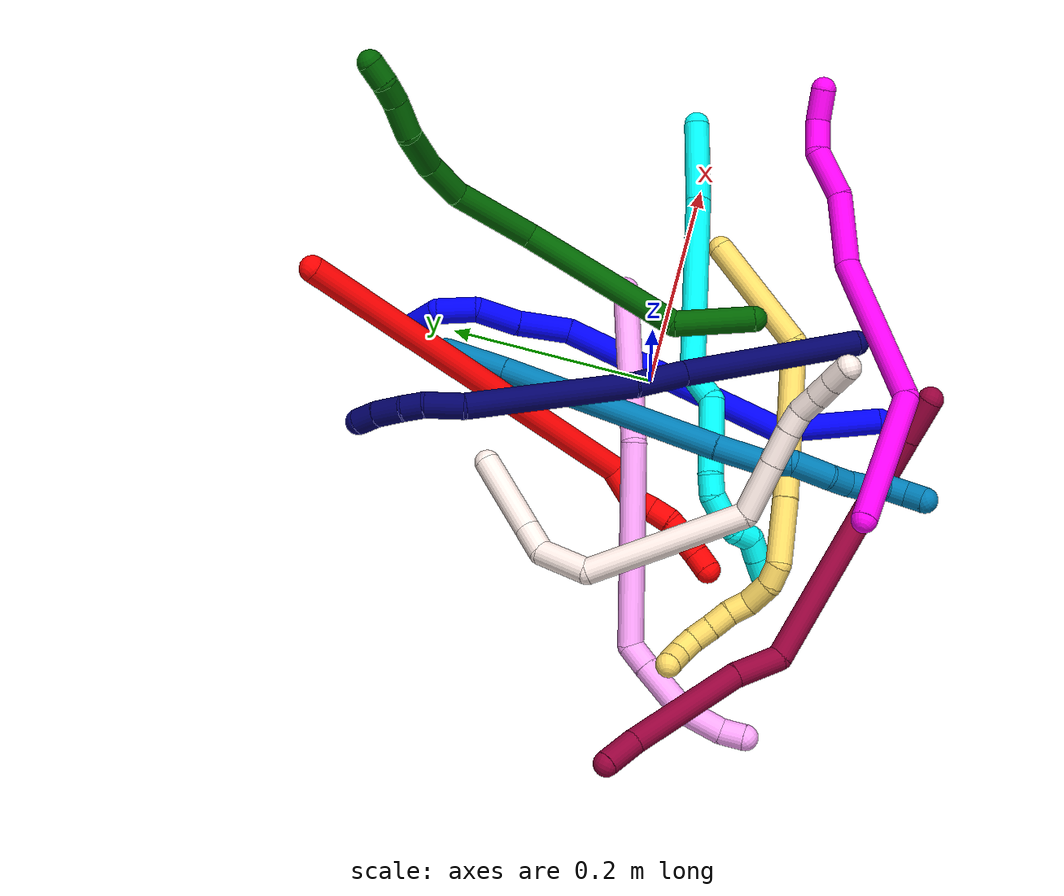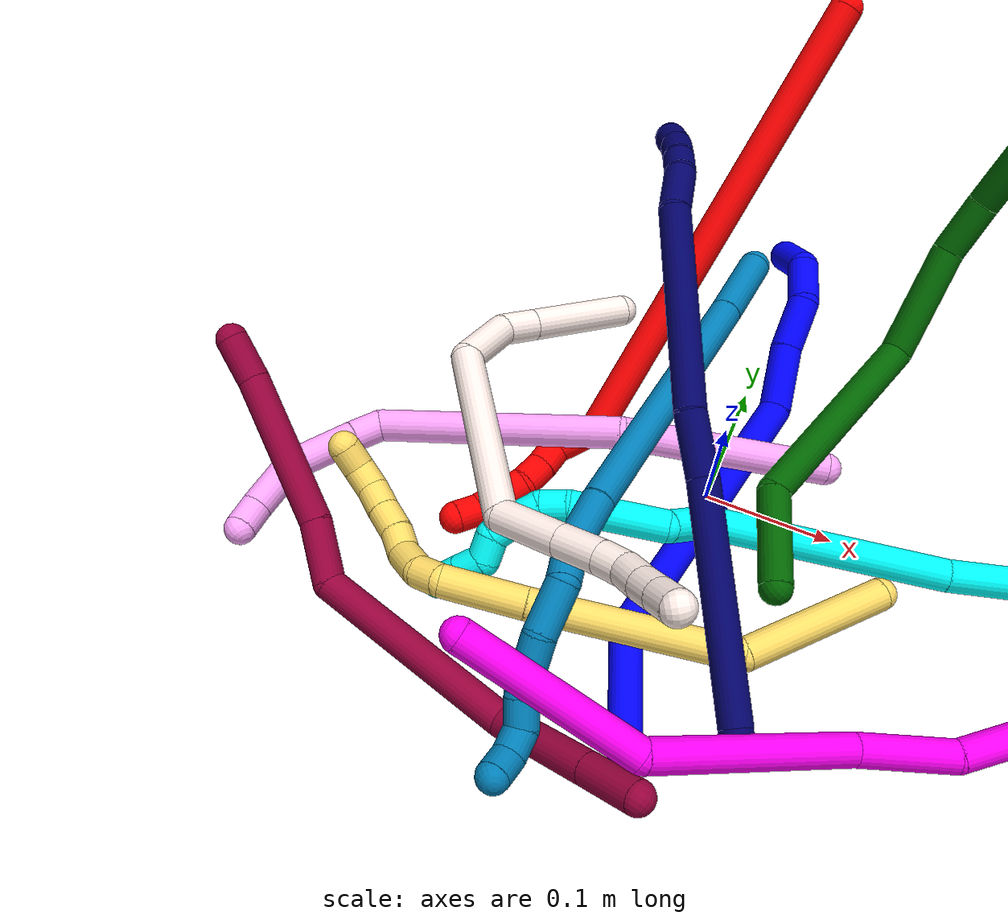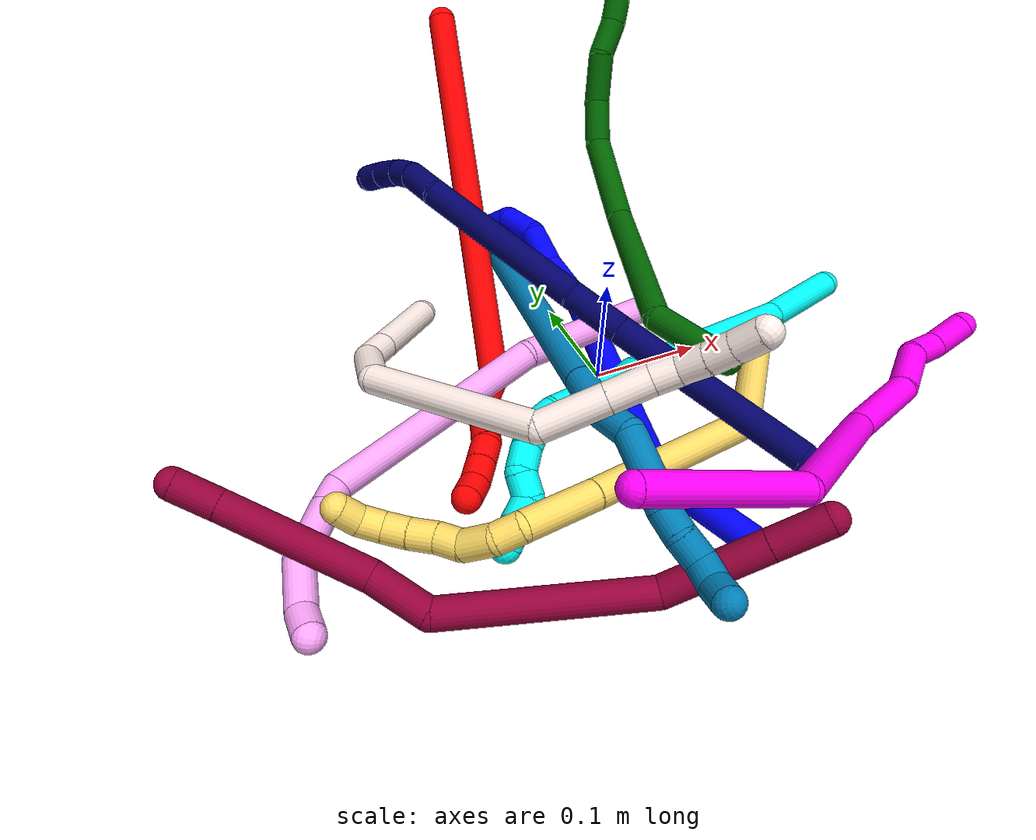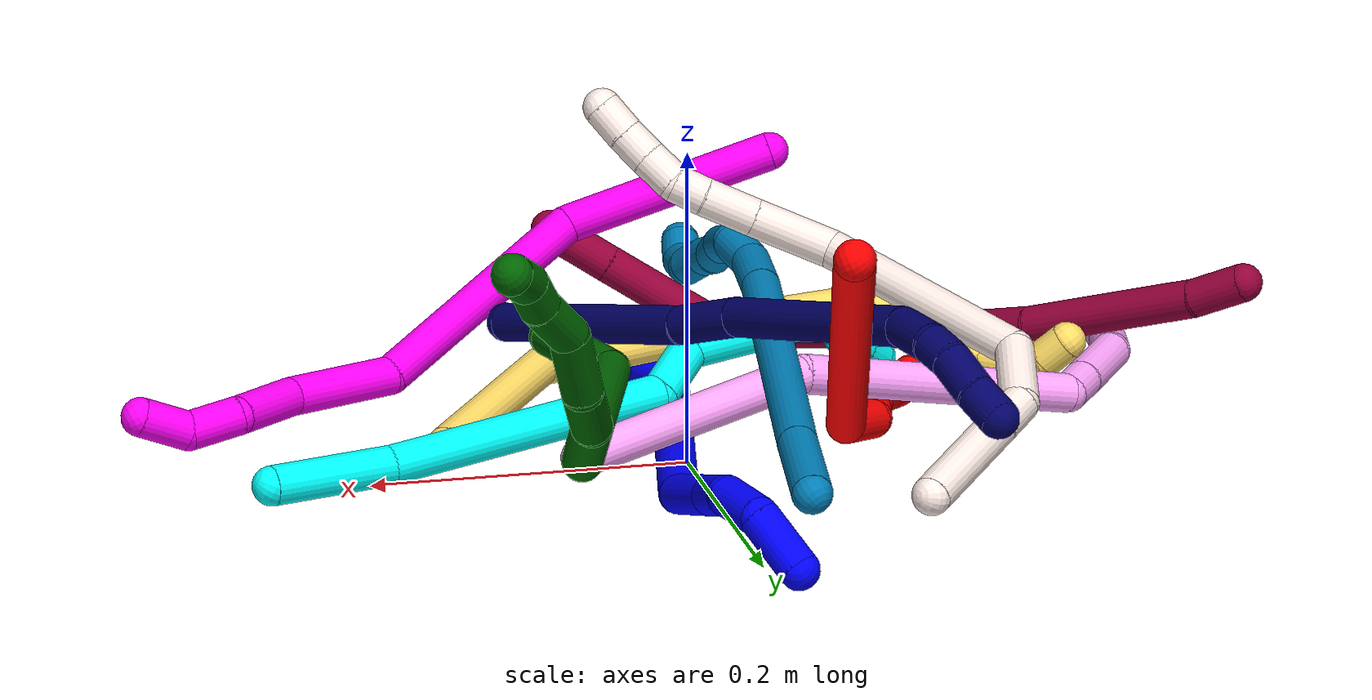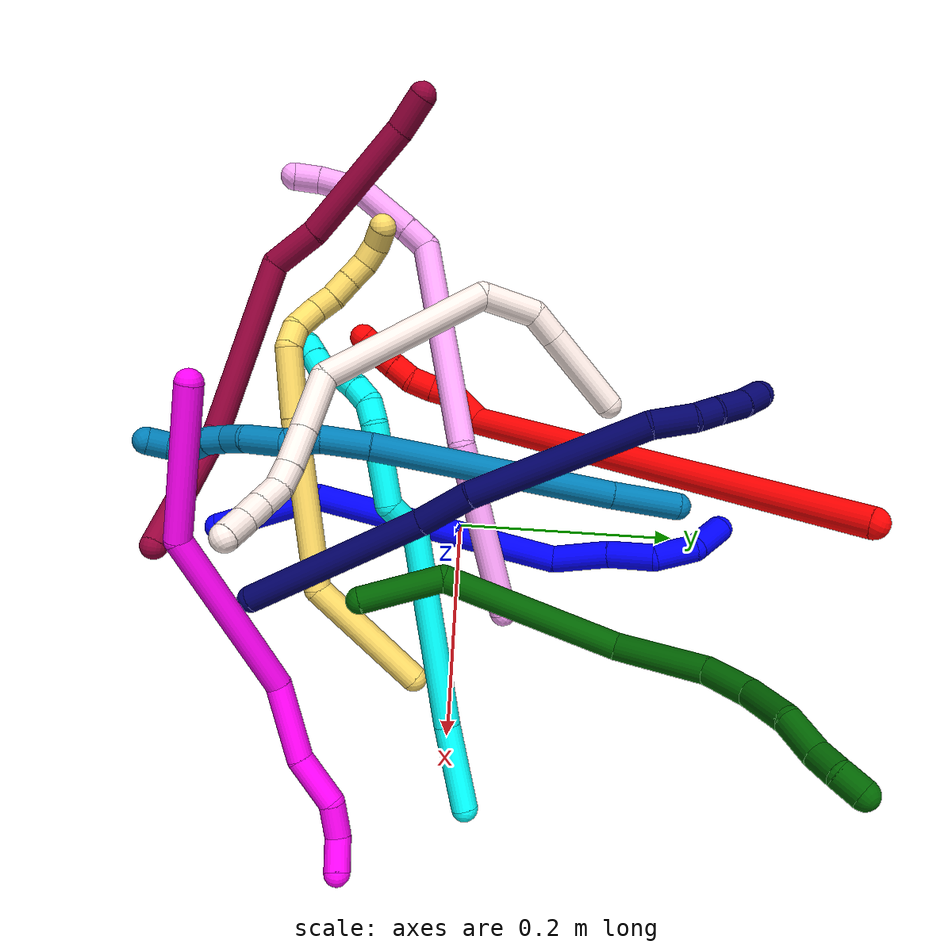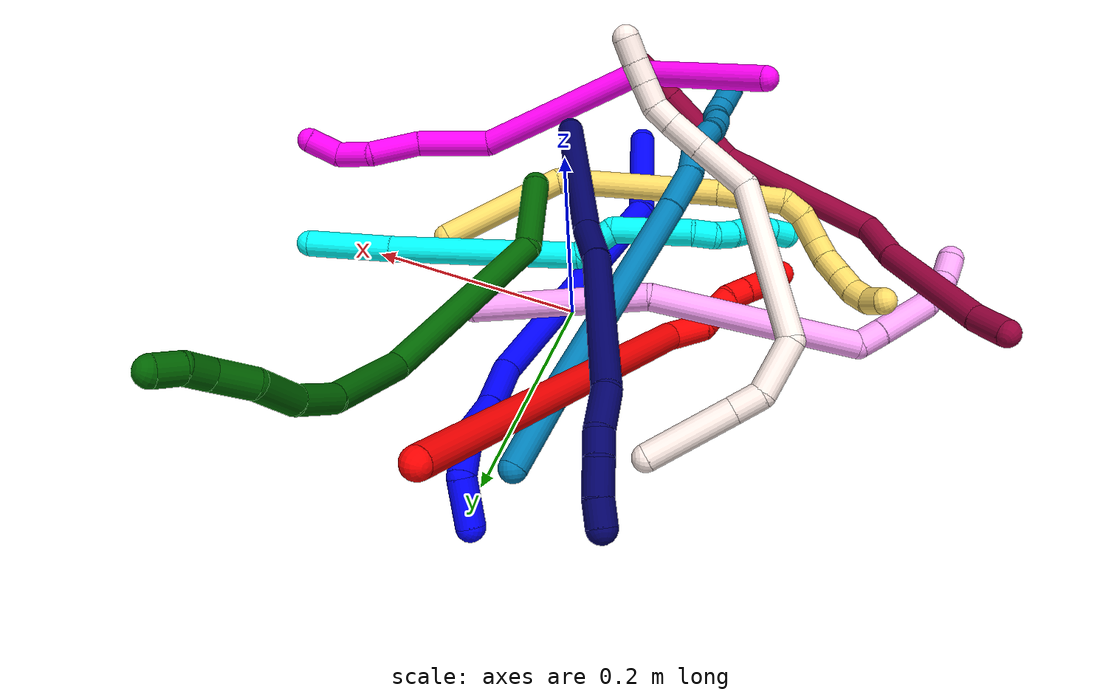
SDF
<sdf version="1.7">
 <world name="default">
  <plugin name="TubeGeneratorPlugin" filename="libtube_generator_plugin.so"/>
  <model name="photoneo_s_sensor">
   <static>1</static>
   <pose>0 0 2 1.57079 1.57079 3.14159</pose>
   <link name="link">
    <inertial><mass>0.1</mass></inertial>
    <sensor name="sensor" type="depth">
     <update_rate>30</update_rate>
     <camera>
      <horizontal_fov>1.22</horizontal_fov>
      <image><width>1920</width><height>1200</height><format>B8G8R8</format></image>
      <clip><near>0.1</near><far>4</far></clip>
      <depth_camera><output>points</output></depth_camera>
     </camera>
     <plugin name="camera_plugin" filename="libgazebo_ros_depth_camera.so">
      <baseline>0.2</baseline>
      <alwaysOn>1</alwaysOn>
      <updateRate>0.0</updateRate>
      <cameraName>camera_ir</cameraName>
      <imageTopicName>/camera/color/image_raw</imageTopicName>
      <cameraInfoTopicName>/camera/color/camera_info</cameraInfoTopicName>
      <depthImageTopicName>/camera/depth/image_raw</depthImageTopicName>
      <depthImageCameraInfoTopicName>/camera/depth/camera_info</depthImageCameraInfoTopicName>
      <pointCloudTopicName>/camera/depth/points</pointCloudTopicName>
      <frameName>fr_optical</frameName>
      <pointCloudCutoff>0.1</pointCloudCutoff>
      <pointCloudCutoffMax>2.0</pointCloudCutoffMax>
      <distortionK1>0</distortionK1>
      <distortionK2>0</distortionK2>
      <distortionK3>0</distortionK3>
      <distortionT1>0</distortionT1>
      <distortionT2>0</distortionT2>
      <CxPrime>0</CxPrime>
      <Cx>0</Cx>
      <Cy>0</Cy>
      <focalLength>0</focalLength>
      <hackBaseline>0</hackBaseline>
     </plugin>
    </sensor>
   </link>
  </model>
  <gravity>0 0 -9.8</gravity>
  <magnetic_field>6e-06 2.3e-05 -4.2e-05</magnetic_field>
  <atmosphere type="adiabatic"/>
  <physics name="default_physics" default="0" type="ode">
   <max_step_size>0.003</max_step_size>
   <real_time_factor>1</real_time_factor>
   <real_time_update_rate>1000</real_time_update_rate>
   <max_contacts>10000</max_contacts>
   <ode>
    <solver>
     <type>quick</type>
     <iters>100</iters>
     <sor>1.3</sor>
     <use_dynamic_moi_rescaling>0</use_dynamic_moi_rescaling>
    </solver>
    <constraints>
     <contact_max_correcting_vel>0</contact_max_correcting_vel>
     <contact_surface_layer>0.001</contact_surface_layer>
     <cfm>0</cfm>
     <erp>0.2</erp>
    </constraints>
   </ode>
  </physics>
  <scene><ambient>0.4 0.4 0.4 1</ambient><background>0.7 0.7 0.7 1</background><shadows>0</shadows></scene>
  <audio><device>default</device></audio>
  <spherical_coordinates>
   <surface_model>EARTH_WGS84</surface_model>
   <latitude_deg>0</latitude_deg>
   <longitude_deg>0</longitude_deg>
   <elevation>0</elevation>
   <heading_deg>0</heading_deg>
  </spherical_coordinates>
  <model name="bin">
   <static>1</static>
   <link name="bottom">
    <collision name="collision-bottom">
     <pose>0 0 -0.01 0 -0 0</pose>
     <geometry><box><size>0.8 0.6 0.02</size></box></geometry>
     <surface>
      <friction><ode><mu>100</mu><mu2>100</mu2></ode></friction>
      <contact><collide_bitmask>65535</collide_bitmask></contact>
     </surface>
    </collision>
   </link>
   <link name="west_wall">
    <collision name="collision-west_wall">
     <pose>-0.41 0 0.1 0 -0 0</pose>
     <geometry><box><size>0.02 0.6 0.2</size></box></geometry>
     <surface>
      <friction><ode><mu>100</mu><mu2>100</mu2></ode></friction>
      <contact><collide_bitmask>65535</collide_bitmask></contact>
     </surface>
    </collision>
   </link>
   <link name="east_wall">
    <collision name="collision-east_wall">
     <pose>0.41 0 0.1 0 -0 0</pose>
     <geometry><box><size>0.02 0.6 0.2</size></box></geometry>
     <surface>
      <friction><ode><mu>100</mu><mu2>100</mu2></ode></friction>
      <contact><collide_bitmask>65535</collide_bitmask></contact>
     </surface>
    </collision>
   </link>
   <link name="south_wall">
    <collision name="collision-south_wall">
     <pose>0 -0.31 0.1 0 -0 0</pose>
     <geometry><box><size>0.8 0.02 0.2</size></box></geometry>
     <surface>
      <friction><ode><mu>100</mu><mu2>100</mu2></ode></friction>
      <contact><collide_bitmask>65535</collide_bitmask></contact>
     </surface>
    </collision>
   </link>
   <link name="north_wall">
    <collision name="collision-north_wall">
     <pose>0 0.31 0.1 0 -0 0</pose>
     <geometry><box><size>0.8 0.02 0.2</size></box></geometry>
     <surface>
      <friction><ode><mu>100</mu><mu2>100</mu2></ode></friction>
      <contact><collide_bitmask>65535</collide_bitmask></contact>
     </surface>
    </collision>
   </link>
  </model>
  <model name="1">
   <static>0</static>
   <link name="1">
    <collision name="collision-cylinder-e_1_1_4">
     <pose>-0.012604 0.040449 0.024734 -1.02197 -0.259829 0.146238</pose>
     <geometry><cylinder><radius>0.0125</radius><length>0.098118</length></cylinder></geometry>
     <surface>
      <friction><ode><mu>1.16</mu><mu2>1.16</mu2><slip1>0</slip1><slip2>0</slip2></ode></friction>
      <contact><ode><kp>1e+06</kp><kd>1</kd><max_vel>0</max_vel><min_depth>0.001</min_depth></ode></contact>
     </surface>
    </collision>
    <visual name="visual-cylinder-e_1_1_4">
     <pose>-0.012604 0.040449 0.024734 -1.02197 -0.259829 0.146238</pose>
     <geometry><cylinder><radius>0.0125</radius><length>0.098118</length></cylinder></geometry>
     <material><ambient>0 0 1 1</ambient></material>
    </visual>
    <collision name="collision-cylinder-e_2_4_5">
     <pose>-0.001591 0.156109 0.131781 -0.740343 0.208727 -0.081249</pose>
     <geometry><cylinder><radius>0.0125</radius><length>0.227944</length></cylinder></geometry>
     <surface>
      <friction><ode><mu>1.16</mu><mu2>1.16</mu2><slip1>0</slip1><slip2>0</slip2></ode></friction>
      <contact><ode><kp>1e+06</kp><kd>1</kd><max_vel>0</max_vel><min_depth>0.001</min_depth></ode></contact>
     </surface>
    </collision>
    <visual name="visual-cylinder-e_2_4_5">
     <pose>-0.001591 0.156109 0.131781 -0.740343 0.208727 -0.081249</pose>
     <geometry><cylinder><radius>0.0125</radius><length>0.227944</length></cylinder></geometry>
     <material><ambient>0 0 1 1</ambient></material>
    </visual>
    <collision name="collision-cylinder-e_3_5_6">
     <pose>0.015587 0.247237 0.233793 -0.679602 -0.248928 0.088399</pose>
     <geometry><cylinder><radius>0.0125</radius><length>0.052265</length></cylinder></geometry>
     <surface>
      <friction><ode><mu>1.16</mu><mu2>1.16</mu2><slip1>0</slip1><slip2>0</slip2></ode></friction>
      <contact><ode><kp>1e+06</kp><kd>1</kd><max_vel>0</max_vel><min_depth>0.001</min_depth></ode></contact>
     </surface>
    </collision>
    <visual name="visual-cylinder-e_3_5_6">
     <pose>0.015587 0.247237 0.233793 -0.679602 -0.248928 0.088399</pose>
     <geometry><cylinder><radius>0.0125</radius><length>0.052265</length></cylinder></geometry>
     <material><ambient>0 0 1 1</ambient></material>
    </visual>
    <collision name="collision-cylinder-e_4_6_7">
     <pose>0.006537 0.274478 0.271198 -0.569 -0.123623 0.036194</pose>
     <geometry><cylinder><radius>0.0125</radius><length>0.042355</length></cylinder></geometry>
     <surface>
      <friction><ode><mu>1.16</mu><mu2>1.16</mu2><slip1>0</slip1><slip2>0</slip2></ode></friction>
      <contact><ode><kp>1e+06</kp><kd>1</kd><max_vel>0</max_vel><min_depth>0.001</min_depth></ode></contact>
     </surface>
    </collision>
    <visual name="visual-cylinder-e_4_6_7">
     <pose>0.006537 0.274478 0.271198 -0.569 -0.123623 0.036194</pose>
     <geometry><cylinder><radius>0.0125</radius><length>0.042355</length></cylinder></geometry>
     <material><ambient>0 0 1 1</ambient></material>
    </visual>
    <collision name="collision-cylinder-e_5_7_8">
     <pose>0.000444 0.301984 0.298541 -1.03362 -0.182818 0.104098</pose>
     <geometry><cylinder><radius>0.0125</radius><length>0.038309</length></cylinder></geometry>
     <surface>
      <friction><ode><mu>1.16</mu><mu2>1.16</mu2><slip1>0</slip1><slip2>0</slip2></ode></friction>
      <contact><ode><kp>1e+06</kp><kd>1</kd><max_vel>0</max_vel><min_depth>0.001</min_depth></ode></contact>
     </surface>
    </collision>
    <visual name="visual-cylinder-e_5_7_8">
     <pose>0.000444 0.301984 0.298541 -1.03362 -0.182818 0.104098</pose>
     <geometry><cylinder><radius>0.0125</radius><length>0.038309</length></cylinder></geometry>
     <material><ambient>0 0 1 1</ambient></material>
    </visual>
    <collision name="collision-cylinder-e_6_8_2">
     <pose>-0.003802 0.338472 0.305439 -1.7049 -0.03724 0.0426</pose>
     <geometry><cylinder><radius>0.0125</radius><length>0.041008</length></cylinder></geometry>
     <surface>
      <friction><ode><mu>1.16</mu><mu2>1.16</mu2><slip1>0</slip1><slip2>0</slip2></ode></friction>
      <contact><ode><kp>1e+06</kp><kd>1</kd><max_vel>0</max_vel><min_depth>0.001</min_depth></ode></contact>
     </surface>
    </collision>
    <visual name="visual-cylinder-e_6_8_2">
     <pose>-0.003802 0.338472 0.305439 -1.7049 -0.03724 0.0426</pose>
     <geometry><cylinder><radius>0.0125</radius><length>0.041008</length></cylinder></geometry>
     <material><ambient>0 0 1 1</ambient></material>
    </visual>
    <collision name="collision-sphere-2">
     <pose>-0.004565 0.358778 0.3027 0 -0 0</pose>
     <geometry><sphere><radius>0.0125</radius></sphere></geometry>
     <surface>
      <friction><ode><mu>1.16</mu><mu2>1.16</mu2><slip1>0</slip1><slip2>0</slip2></ode></friction>
      <contact><ode><kp>1e+06</kp><kd>1</kd><max_vel>0</max_vel><min_depth>0.001</min_depth></ode></contact>
     </surface>
    </collision>
    <visual name="visual-sphere-2">
     <pose>-0.004565 0.358778 0.3027 0 -0 0</pose>
     <geometry><sphere><radius>0.0125</radius></sphere></geometry>
     <material><ambient>0 0 1 1</ambient></material>
    </visual>
    <collision name="collision-sphere-4">
     <pose>-0.025208 0.080899 0.049469 0 -0 0</pose>
     <geometry><sphere><radius>0.0125</radius></sphere></geometry>
     <surface>
      <friction><ode><mu>1.16</mu><mu2>1.16</mu2><slip1>0</slip1><slip2>0</slip2></ode></friction>
      <contact><ode><kp>1e+06</kp><kd>1</kd><max_vel>0</max_vel><min_depth>0.001</min_depth></ode></contact>
     </surface>
    </collision>
    <visual name="visual-sphere-4">
     <pose>-0.025208 0.080899 0.049469 0 -0 0</pose>
     <geometry><sphere><radius>0.0125</radius></sphere></geometry>
     <material><ambient>0 0 1 1</ambient></material>
    </visual>
    <collision name="collision-sphere-1">
     <geometry><sphere><radius>0.0125</radius></sphere></geometry>
     <surface>
      <friction><ode><mu>1.16</mu><mu2>1.16</mu2><slip1>0</slip1><slip2>0</slip2></ode></friction>
      <contact><ode><kp>1e+06</kp><kd>1</kd><max_vel>0</max_vel><min_depth>0.001</min_depth></ode></contact>
     </surface>
    </collision>
    <visual name="visual-sphere-1">
     <geometry><sphere><radius>0.0125</radius></sphere></geometry>
     <material><ambient>0 0 1 1</ambient></material>
    </visual>
    <collision name="collision-sphere-8">
     <pose>-0.003038 0.318166 0.308179 0 -0 0</pose>
     <geometry><sphere><radius>0.0125</radius></sphere></geometry>
     <surface>
      <friction><ode><mu>1.16</mu><mu2>1.16</mu2><slip1>0</slip1><slip2>0</slip2></ode></friction>
      <contact><ode><kp>1e+06</kp><kd>1</kd><max_vel>0</max_vel><min_depth>0.001</min_depth></ode></contact>
     </surface>
    </collision>
    <visual name="visual-sphere-8">
     <pose>-0.003038 0.318166 0.308179 0 -0 0</pose>
     <geometry><sphere><radius>0.0125</radius></sphere></geometry>
     <material><ambient>0 0 1 1</ambient></material>
    </visual>
    <collision name="collision-sphere-5">
     <pose>0.022025 0.231319 0.214093 0 -0 0</pose>
     <geometry><sphere><radius>0.0125</radius></sphere></geometry>
     <surface>
      <friction><ode><mu>1.16</mu><mu2>1.16</mu2><slip1>0</slip1><slip2>0</slip2></ode></friction>
      <contact><ode><kp>1e+06</kp><kd>1</kd><max_vel>0</max_vel><min_depth>0.001</min_depth></ode></contact>
     </surface>
    </collision>
    <visual name="visual-sphere-5">
     <pose>0.022025 0.231319 0.214093 0 -0 0</pose>
     <geometry><sphere><radius>0.0125</radius></sphere></geometry>
     <material><ambient>0 0 1 1</ambient></material>
    </visual>
    <collision name="collision-sphere-6">
     <pose>0.009149 0.263155 0.253493 0 -0 0</pose>
     <geometry><sphere><radius>0.0125</radius></sphere></geometry>
     <surface>
      <friction><ode><mu>1.16</mu><mu2>1.16</mu2><slip1>0</slip1><slip2>0</slip2></ode></friction>
      <contact><ode><kp>1e+06</kp><kd>1</kd><max_vel>0</max_vel><min_depth>0.001</min_depth></ode></contact>
     </surface>
    </collision>
    <visual name="visual-sphere-6">
     <pose>0.009149 0.263155 0.253493 0 -0 0</pose>
     <geometry><sphere><radius>0.0125</radius></sphere></geometry>
     <material><ambient>0 0 1 1</ambient></material>
    </visual>
    <collision name="collision-sphere-7">
     <pose>0.003926 0.285801 0.288903 0 -0 0</pose>
     <geometry><sphere><radius>0.0125</radius></sphere></geometry>
     <surface>
      <friction><ode><mu>1.16</mu><mu2>1.16</mu2><slip1>0</slip1><slip2>0</slip2></ode></friction>
      <contact><ode><kp>1e+06</kp><kd>1</kd><max_vel>0</max_vel><min_depth>0.001</min_depth></ode></contact>
     </surface>
    </collision>
    <visual name="visual-sphere-7">
     <pose>0.003926 0.285801 0.288903 0 -0 0</pose>
     <geometry><sphere><radius>0.0125</radius></sphere></geometry>
     <material><ambient>0 0 1 1</ambient></material>
    </visual>
    <inertial>
     <pose>-0.001294 0.179098 0.160267 0 -0 0</pose>
     <mass>0.5</mass>
     <inertia>
      <ixx>0.001019</ixx>
      <ixy>0</ixy>
      <ixz>0</ixz>
      <iyy>0.000772</iyy>
      <iyz>0</iyz>
      <izz>-0.000906</izz>
     </inertia>
    </inertial>
   </link>
   <pose>0.014996 -0.226043 0.011495 -0.705297 0.535129 0.046117</pose>
  </model>
  <model name="2">
   <static>0</static>
   <link name="2">
    <collision name="collision-cylinder-e_1_1_4">
     <pose>-0.047074 -0.161714 -0.067731 1.96743 -0.262311 -0.391454</pose>
     <geometry><cylinder><radius>0.0125</radius><length>0.36307</length></cylinder></geometry>
     <surface>
      <friction><ode><mu>1.16</mu><mu2>1.16</mu2><slip1>0</slip1><slip2>0</slip2></ode></friction>
      <contact><ode><kp>1e+06</kp><kd>1</kd><max_vel>0</max_vel><min_depth>0.001</min_depth></ode></contact>
     </surface>
    </collision>
    <visual name="visual-cylinder-e_1_1_4">
     <pose>-0.047074 -0.161714 -0.067731 1.96743 -0.262311 -0.391454</pose>
     <geometry><cylinder><radius>0.0125</radius><length>0.36307</length></cylinder></geometry>
     <material><ambient>1 0 0 1</ambient></material>
    </visual>
    <collision name="collision-cylinder-e_2_4_5">
     <pose>-0.09661 -0.340525 -0.131635 1.35058 -0.139572 -0.111848</pose>
     <geometry><cylinder><radius>0.0125</radius><length>0.035385</length></cylinder></geometry>
     <surface>
      <friction><ode><mu>1.16</mu><mu2>1.16</mu2><slip1>0</slip1><slip2>0</slip2></ode></friction>
      <contact><ode><kp>1e+06</kp><kd>1</kd><max_vel>0</max_vel><min_depth>0.001</min_depth></ode></contact>
     </surface>
    </collision>
    <visual name="visual-cylinder-e_2_4_5">
     <pose>-0.09661 -0.340525 -0.131635 1.35058 -0.139572 -0.111848</pose>
     <geometry><cylinder><radius>0.0125</radius><length>0.035385</length></cylinder></geometry>
     <material><ambient>1 0 0 1</ambient></material>
    </visual>
    <collision name="collision-cylinder-e_3_5_6">
     <pose>-0.096536 -0.367256 -0.129548 1.74947 0.253436 0.302609</pose>
     <geometry><cylinder><radius>0.0125</radius><length>0.020225</length></cylinder></geometry>
     <surface>
      <friction><ode><mu>1.16</mu><mu2>1.16</mu2><slip1>0</slip1><slip2>0</slip2></ode></friction>
      <contact><ode><kp>1e+06</kp><kd>1</kd><max_vel>0</max_vel><min_depth>0.001</min_depth></ode></contact>
     </surface>
    </collision>
    <visual name="visual-cylinder-e_3_5_6">
     <pose>-0.096536 -0.367256 -0.129548 1.74947 0.253436 0.302609</pose>
     <geometry><cylinder><radius>0.0125</radius><length>0.020225</length></cylinder></geometry>
     <material><ambient>1 0 0 1</ambient></material>
    </visual>
    <collision name="collision-cylinder-e_4_6_7">
     <pose>-0.091079 -0.386931 -0.131534 1.59529 0.283042 0.289963</pose>
     <geometry><cylinder><radius>0.0125</radius><length>0.020922</length></cylinder></geometry>
     <surface>
      <friction><ode><mu>1.16</mu><mu2>1.16</mu2><slip1>0</slip1><slip2>0</slip2></ode></friction>
      <contact><ode><kp>1e+06</kp><kd>1</kd><max_vel>0</max_vel><min_depth>0.001</min_depth></ode></contact>
     </surface>
    </collision>
    <visual name="visual-cylinder-e_4_6_7">
     <pose>-0.091079 -0.386931 -0.131534 1.59529 0.283042 0.289963</pose>
     <geometry><cylinder><radius>0.0125</radius><length>0.020922</length></cylinder></geometry>
     <material><ambient>1 0 0 1</ambient></material>
    </visual>
    <collision name="collision-cylinder-e_5_7_8">
     <pose>-0.088606 -0.407045 -0.130417 1.43636 -0.044112 -0.038549</pose>
     <geometry><cylinder><radius>0.0125</radius><length>0.020349</length></cylinder></geometry>
     <surface>
      <friction><ode><mu>1.16</mu><mu2>1.16</mu2><slip1>0</slip1><slip2>0</slip2></ode></friction>
      <contact><ode><kp>1e+06</kp><kd>1</kd><max_vel>0</max_vel><min_depth>0.001</min_depth></ode></contact>
     </surface>
    </collision>
    <visual name="visual-cylinder-e_5_7_8">
     <pose>-0.088606 -0.407045 -0.130417 1.43636 -0.044112 -0.038549</pose>
     <geometry><cylinder><radius>0.0125</radius><length>0.020349</length></cylinder></geometry>
     <material><ambient>1 0 0 1</ambient></material>
    </visual>
    <collision name="collision-cylinder-e_6_8_9">
     <pose>-0.089623 -0.427004 -0.127632 1.42788 -0.056832 -0.049243</pose>
     <geometry><cylinder><radius>0.0125</radius><length>0.020009</length></cylinder></geometry>
     <surface>
      <friction><ode><mu>1.16</mu><mu2>1.16</mu2><slip1>0</slip1><slip2>0</slip2></ode></friction>
      <contact><ode><kp>1e+06</kp><kd>1</kd><max_vel>0</max_vel><min_depth>0.001</min_depth></ode></contact>
     </surface>
    </collision>
    <visual name="visual-cylinder-e_6_8_9">
     <pose>-0.089623 -0.427004 -0.127632 1.42788 -0.056832 -0.049243</pose>
     <geometry><cylinder><radius>0.0125</radius><length>0.020009</length></cylinder></geometry>
     <material><ambient>1 0 0 1</ambient></material>
    </visual>
    <collision name="collision-cylinder-e_7_9_2">
     <pose>-0.088365 -0.446067 -0.122621 1.19798 0.183294 0.125314</pose>
     <geometry><cylinder><radius>0.0125</radius><length>0.020042</length></cylinder></geometry>
     <surface>
      <friction><ode><mu>1.16</mu><mu2>1.16</mu2><slip1>0</slip1><slip2>0</slip2></ode></friction>
      <contact><ode><kp>1e+06</kp><kd>1</kd><max_vel>0</max_vel><min_depth>0.001</min_depth></ode></contact>
     </surface>
    </collision>
    <visual name="visual-cylinder-e_7_9_2">
     <pose>-0.088365 -0.446067 -0.122621 1.19798 0.183294 0.125314</pose>
     <geometry><cylinder><radius>0.0125</radius><length>0.020042</length></cylinder></geometry>
     <material><ambient>1 0 0 1</ambient></material>
    </visual>
    <collision name="collision-sphere-2">
     <pose>-0.086538 -0.455243 -0.119032 0 -0 0</pose>
     <geometry><sphere><radius>0.0125</radius></sphere></geometry>
     <surface>
      <friction><ode><mu>1.16</mu><mu2>1.16</mu2><slip1>0</slip1><slip2>0</slip2></ode></friction>
      <contact><ode><kp>1e+06</kp><kd>1</kd><max_vel>0</max_vel><min_depth>0.001</min_depth></ode></contact>
     </surface>
    </collision>
    <visual name="visual-sphere-2">
     <pose>-0.086538 -0.455243 -0.119032 0 -0 0</pose>
     <geometry><sphere><radius>0.0125</radius></sphere></geometry>
     <material><ambient>1 0 0 1</ambient></material>
    </visual>
    <collision name="collision-sphere-9">
     <pose>-0.090191 -0.436891 -0.12621 0 -0 0</pose>
     <geometry><sphere><radius>0.0125</radius></sphere></geometry>
     <surface>
      <friction><ode><mu>1.16</mu><mu2>1.16</mu2><slip1>0</slip1><slip2>0</slip2></ode></friction>
      <contact><ode><kp>1e+06</kp><kd>1</kd><max_vel>0</max_vel><min_depth>0.001</min_depth></ode></contact>
     </surface>
    </collision>
    <visual name="visual-sphere-9">
     <pose>-0.090191 -0.436891 -0.12621 0 -0 0</pose>
     <geometry><sphere><radius>0.0125</radius></sphere></geometry>
     <material><ambient>1 0 0 1</ambient></material>
    </visual>
    <collision name="collision-sphere-4">
     <pose>-0.094149 -0.323428 -0.135463 0 -0 0</pose>
     <geometry><sphere><radius>0.0125</radius></sphere></geometry>
     <surface>
      <friction><ode><mu>1.16</mu><mu2>1.16</mu2><slip1>0</slip1><slip2>0</slip2></ode></friction>
      <contact><ode><kp>1e+06</kp><kd>1</kd><max_vel>0</max_vel><min_depth>0.001</min_depth></ode></contact>
     </surface>
    </collision>
    <visual name="visual-sphere-4">
     <pose>-0.094149 -0.323428 -0.135463 0 -0 0</pose>
     <geometry><sphere><radius>0.0125</radius></sphere></geometry>
     <material><ambient>1 0 0 1</ambient></material>
    </visual>
    <collision name="collision-sphere-1">
     <geometry><sphere><radius>0.0125</radius></sphere></geometry>
     <surface>
      <friction><ode><mu>1.16</mu><mu2>1.16</mu2><slip1>0</slip1><slip2>0</slip2></ode></friction>
      <contact><ode><kp>1e+06</kp><kd>1</kd><max_vel>0</max_vel><min_depth>0.001</min_depth></ode></contact>
     </surface>
    </collision>
    <visual name="visual-sphere-1">
     <geometry><sphere><radius>0.0125</radius></sphere></geometry>
     <material><ambient>1 0 0 1</ambient></material>
    </visual>
    <collision name="collision-sphere-8">
     <pose>-0.089055 -0.417118 -0.129055 0 -0 0</pose>
     <geometry><sphere><radius>0.0125</radius></sphere></geometry>
     <surface>
      <friction><ode><mu>1.16</mu><mu2>1.16</mu2><slip1>0</slip1><slip2>0</slip2></ode></friction>
      <contact><ode><kp>1e+06</kp><kd>1</kd><max_vel>0</max_vel><min_depth>0.001</min_depth></ode></contact>
     </surface>
    </collision>
    <visual name="visual-sphere-8">
     <pose>-0.089055 -0.417118 -0.129055 0 -0 0</pose>
     <geometry><sphere><radius>0.0125</radius></sphere></geometry>
     <material><ambient>1 0 0 1</ambient></material>
    </visual>
    <collision name="collision-sphere-5">
     <pose>-0.099071 -0.357622 -0.127808 0 -0 0</pose>
     <geometry><sphere><radius>0.0125</radius></sphere></geometry>
     <surface>
      <friction><ode><mu>1.16</mu><mu2>1.16</mu2><slip1>0</slip1><slip2>0</slip2></ode></friction>
      <contact><ode><kp>1e+06</kp><kd>1</kd><max_vel>0</max_vel><min_depth>0.001</min_depth></ode></contact>
     </surface>
    </collision>
    <visual name="visual-sphere-5">
     <pose>-0.099071 -0.357622 -0.127808 0 -0 0</pose>
     <geometry><sphere><radius>0.0125</radius></sphere></geometry>
     <material><ambient>1 0 0 1</ambient></material>
    </visual>
    <collision name="collision-sphere-6">
     <pose>-0.094 -0.376889 -0.131288 0 -0 0</pose>
     <geometry><sphere><radius>0.0125</radius></sphere></geometry>
     <surface>
      <friction><ode><mu>1.16</mu><mu2>1.16</mu2><slip1>0</slip1><slip2>0</slip2></ode></friction>
      <contact><ode><kp>1e+06</kp><kd>1</kd><max_vel>0</max_vel><min_depth>0.001</min_depth></ode></contact>
     </surface>
    </collision>
    <visual name="visual-sphere-6">
     <pose>-0.094 -0.376889 -0.131288 0 -0 0</pose>
     <geometry><sphere><radius>0.0125</radius></sphere></geometry>
     <material><ambient>1 0 0 1</ambient></material>
    </visual>
    <collision name="collision-sphere-7">
     <pose>-0.088157 -0.396972 -0.13178 0 -0 0</pose>
     <geometry><sphere><radius>0.0125</radius></sphere></geometry>
     <surface>
      <friction><ode><mu>1.16</mu><mu2>1.16</mu2><slip1>0</slip1><slip2>0</slip2></ode></friction>
      <contact><ode><kp>1e+06</kp><kd>1</kd><max_vel>0</max_vel><min_depth>0.001</min_depth></ode></contact>
     </surface>
    </collision>
    <visual name="visual-sphere-7">
     <pose>-0.088157 -0.396972 -0.13178 0 -0 0</pose>
     <geometry><sphere><radius>0.0125</radius></sphere></geometry>
     <material><ambient>1 0 0 1</ambient></material>
    </visual>
    <inertial>
     <pose>-0.05947 -0.224105 -0.084572 0 -0 0</pose>
     <mass>0.5</mass>
     <inertia>
      <ixx>0.002104</ixx>
      <ixy>0</ixy>
      <ixz>0</ixz>
      <iyy>-0.002572</iyy>
      <iyz>0</iyz>
      <izz>0.004606</izz>
     </inertia>
    </inertial>
   </link>
   <pose>-0.027079 0.307935 0.219072 0.337003 -1.05977 -0.783245</pose>
  </model>
  <model name="3">
   <static>0</static>
   <link name="3">
    <collision name="collision-cylinder-e_1_1_4">
     <pose>-0.020968 -0.000789 -0.034111 3.11846 -0.551033 -3.05981</pose>
     <geometry><cylinder><radius>0.0125</radius><length>0.080095</length></cylinder></geometry>
     <surface>
      <friction><ode><mu>1.16</mu><mu2>1.16</mu2><slip1>0</slip1><slip2>0</slip2></ode></friction>
      <contact><ode><kp>1e+06</kp><kd>1</kd><max_vel>0</max_vel><min_depth>0.001</min_depth></ode></contact>
     </surface>
    </collision>
    <visual name="visual-cylinder-e_1_1_4">
     <pose>-0.020968 -0.000789 -0.034111 3.11846 -0.551033 -3.05981</pose>
     <geometry><cylinder><radius>0.0125</radius><length>0.080095</length></cylinder></geometry>
     <material><ambient>0.003922 1 0.996078 1</ambient></material>
    </visual>
    <collision name="collision-cylinder-e_2_4_5">
     <pose>-0.095569 0.005714 -0.142566 -3.04381 -0.622687 2.83982</pose>
     <geometry><cylinder><radius>0.0125</radius><length>0.183923</length></cylinder></geometry>
     <surface>
      <friction><ode><mu>1.16</mu><mu2>1.16</mu2><slip1>0</slip1><slip2>0</slip2></ode></friction>
      <contact><ode><kp>1e+06</kp><kd>1</kd><max_vel>0</max_vel><min_depth>0.001</min_depth></ode></contact>
     </surface>
    </collision>
    <visual name="visual-cylinder-e_2_4_5">
     <pose>-0.095569 0.005714 -0.142566 -3.04381 -0.622687 2.83982</pose>
     <geometry><cylinder><radius>0.0125</radius><length>0.183923</length></cylinder></geometry>
     <material><ambient>0.003922 1 0.996078 1</ambient></material>
    </visual>
    <collision name="collision-cylinder-e_3_5_6">
     <pose>-0.167815 0.009426 -0.223191 2.62343 -1.20033 -2.40262</pose>
     <geometry><cylinder><radius>0.0125</radius><length>0.039934</length></cylinder></geometry>
     <surface>
      <friction><ode><mu>1.16</mu><mu2>1.16</mu2><slip1>0</slip1><slip2>0</slip2></ode></friction>
      <contact><ode><kp>1e+06</kp><kd>1</kd><max_vel>0</max_vel><min_depth>0.001</min_depth></ode></contact>
     </surface>
    </collision>
    <visual name="visual-cylinder-e_3_5_6">
     <pose>-0.167815 0.009426 -0.223191 2.62343 -1.20033 -2.40262</pose>
     <geometry><cylinder><radius>0.0125</radius><length>0.039934</length></cylinder></geometry>
     <material><ambient>0.003922 1 0.996078 1</ambient></material>
    </visual>
    <collision name="collision-cylinder-e_4_6_7">
     <pose>-0.207806 0.008141 -0.259705 -3.06582 -0.61413 2.90363</pose>
     <geometry><cylinder><radius>0.0125</radius><length>0.074199</length></cylinder></geometry>
     <surface>
      <friction><ode><mu>1.16</mu><mu2>1.16</mu2><slip1>0</slip1><slip2>0</slip2></ode></friction>
      <contact><ode><kp>1e+06</kp><kd>1</kd><max_vel>0</max_vel><min_depth>0.001</min_depth></ode></contact>
     </surface>
    </collision>
    <visual name="visual-cylinder-e_4_6_7">
     <pose>-0.207806 0.008141 -0.259705 -3.06582 -0.61413 2.90363</pose>
     <geometry><cylinder><radius>0.0125</radius><length>0.074199</length></cylinder></geometry>
     <material><ambient>0.003922 1 0.996078 1</ambient></material>
    </visual>
    <collision name="collision-cylinder-e_5_7_8">
     <pose>-0.233387 0.008951 -0.298901 2.97738 -0.433236 -2.42592</pose>
     <geometry><cylinder><radius>0.0125</radius><length>0.020019</length></cylinder></geometry>
     <surface>
      <friction><ode><mu>1.16</mu><mu2>1.16</mu2><slip1>0</slip1><slip2>0</slip2></ode></friction>
      <contact><ode><kp>1e+06</kp><kd>1</kd><max_vel>0</max_vel><min_depth>0.001</min_depth></ode></contact>
     </surface>
    </collision>
    <visual name="visual-cylinder-e_5_7_8">
     <pose>-0.233387 0.008951 -0.298901 2.97738 -0.433236 -2.42592</pose>
     <geometry><cylinder><radius>0.0125</radius><length>0.020019</length></cylinder></geometry>
     <material><ambient>0.003922 1 0.996078 1</ambient></material>
    </visual>
    <collision name="collision-cylinder-e_6_8_9">
     <pose>-0.241061 0.001704 -0.315301 2.48244 -0.35357 -0.962642</pose>
     <geometry><cylinder><radius>0.0125</radius><length>0.020057</length></cylinder></geometry>
     <surface>
      <friction><ode><mu>1.16</mu><mu2>1.16</mu2><slip1>0</slip1><slip2>0</slip2></ode></friction>
      <contact><ode><kp>1e+06</kp><kd>1</kd><max_vel>0</max_vel><min_depth>0.001</min_depth></ode></contact>
     </surface>
    </collision>
    <visual name="visual-cylinder-e_6_8_9">
     <pose>-0.241061 0.001704 -0.315301 2.48244 -0.35357 -0.962642</pose>
     <geometry><cylinder><radius>0.0125</radius><length>0.020057</length></cylinder></geometry>
     <material><ambient>0.003922 1 0.996078 1</ambient></material>
    </visual>
    <collision name="collision-cylinder-e_7_9_10">
     <pose>-0.24876 -0.011288 -0.329388 2.31446 -0.406297 -0.877672</pose>
     <geometry><cylinder><radius>0.0125</radius><length>0.021389</length></cylinder></geometry>
     <surface>
      <friction><ode><mu>1.16</mu><mu2>1.16</mu2><slip1>0</slip1><slip2>0</slip2></ode></friction>
      <contact><ode><kp>1e+06</kp><kd>1</kd><max_vel>0</max_vel><min_depth>0.001</min_depth></ode></contact>
     </surface>
    </collision>
    <visual name="visual-cylinder-e_7_9_10">
     <pose>-0.24876 -0.011288 -0.329388 2.31446 -0.406297 -0.877672</pose>
     <geometry><cylinder><radius>0.0125</radius><length>0.021389</length></cylinder></geometry>
     <material><ambient>0.003922 1 0.996078 1</ambient></material>
    </visual>
    <collision name="collision-cylinder-e_8_10_11">
     <pose>-0.252566 -0.028129 -0.338776 1.84831 0.042066 0.055716</pose>
     <geometry><cylinder><radius>0.0125</radius><length>0.020004</length></cylinder></geometry>
     <surface>
      <friction><ode><mu>1.16</mu><mu2>1.16</mu2><slip1>0</slip1><slip2>0</slip2></ode></friction>
      <contact><ode><kp>1e+06</kp><kd>1</kd><max_vel>0</max_vel><min_depth>0.001</min_depth></ode></contact>
     </surface>
    </collision>
    <visual name="visual-cylinder-e_8_10_11">
     <pose>-0.252566 -0.028129 -0.338776 1.84831 0.042066 0.055716</pose>
     <geometry><cylinder><radius>0.0125</radius><length>0.020004</length></cylinder></geometry>
     <material><ambient>0.003922 1 0.996078 1</ambient></material>
    </visual>
    <collision name="collision-cylinder-e_9_11_12">
     <pose>-0.253533 -0.042901 -0.350134 2.60214 -0.137212 -0.487218</pose>
     <geometry><cylinder><radius>0.0125</radius><length>0.020285</length></cylinder></geometry>
     <surface>
      <friction><ode><mu>1.16</mu><mu2>1.16</mu2><slip1>0</slip1><slip2>0</slip2></ode></friction>
      <contact><ode><kp>1e+06</kp><kd>1</kd><max_vel>0</max_vel><min_depth>0.001</min_depth></ode></contact>
     </surface>
    </collision>
    <visual name="visual-cylinder-e_9_11_12">
     <pose>-0.253533 -0.042901 -0.350134 2.60214 -0.137212 -0.487218</pose>
     <geometry><cylinder><radius>0.0125</radius><length>0.020285</length></cylinder></geometry>
     <material><ambient>0.003922 1 0.996078 1</ambient></material>
    </visual>
    <collision name="collision-cylinder-e_10_12_2">
     <pose>-0.256201 -0.053535 -0.367082 2.5601 -0.12788 -0.421594</pose>
     <geometry><cylinder><radius>0.0125</radius><length>0.020095</length></cylinder></geometry>
     <surface>
      <friction><ode><mu>1.16</mu><mu2>1.16</mu2><slip1>0</slip1><slip2>0</slip2></ode></friction>
      <contact><ode><kp>1e+06</kp><kd>1</kd><max_vel>0</max_vel><min_depth>0.001</min_depth></ode></contact>
     </surface>
    </collision>
    <visual name="visual-cylinder-e_10_12_2">
     <pose>-0.256201 -0.053535 -0.367082 2.5601 -0.12788 -0.421594</pose>
     <geometry><cylinder><radius>0.0125</radius><length>0.020095</length></cylinder></geometry>
     <material><ambient>0.003922 1 0.996078 1</ambient></material>
    </visual>
    <collision name="collision-sphere-2">
     <pose>-0.257483 -0.059009 -0.37541 0 -0 0</pose>
     <geometry><sphere><radius>0.0125</radius></sphere></geometry>
     <surface>
      <friction><ode><mu>1.16</mu><mu2>1.16</mu2><slip1>0</slip1><slip2>0</slip2></ode></friction>
      <contact><ode><kp>1e+06</kp><kd>1</kd><max_vel>0</max_vel><min_depth>0.001</min_depth></ode></contact>
     </surface>
    </collision>
    <visual name="visual-sphere-2">
     <pose>-0.257483 -0.059009 -0.37541 0 -0 0</pose>
     <geometry><sphere><radius>0.0125</radius></sphere></geometry>
     <material><ambient>0.003922 1 0.996078 1</ambient></material>
    </visual>
    <collision name="collision-sphere-12">
     <pose>-0.25492 -0.048061 -0.358755 0 -0 0</pose>
     <geometry><sphere><radius>0.0125</radius></sphere></geometry>
     <surface>
      <friction><ode><mu>1.16</mu><mu2>1.16</mu2><slip1>0</slip1><slip2>0</slip2></ode></friction>
      <contact><ode><kp>1e+06</kp><kd>1</kd><max_vel>0</max_vel><min_depth>0.001</min_depth></ode></contact>
     </surface>
    </collision>
    <visual name="visual-sphere-12">
     <pose>-0.25492 -0.048061 -0.358755 0 -0 0</pose>
     <geometry><sphere><radius>0.0125</radius></sphere></geometry>
     <material><ambient>0.003922 1 0.996078 1</ambient></material>
    </visual>
    <collision name="collision-sphere-11">
     <pose>-0.252145 -0.03774 -0.341514 0 -0 0</pose>
     <geometry><sphere><radius>0.0125</radius></sphere></geometry>
     <surface>
      <friction><ode><mu>1.16</mu><mu2>1.16</mu2><slip1>0</slip1><slip2>0</slip2></ode></friction>
      <contact><ode><kp>1e+06</kp><kd>1</kd><max_vel>0</max_vel><min_depth>0.001</min_depth></ode></contact>
     </surface>
    </collision>
    <visual name="visual-sphere-11">
     <pose>-0.252145 -0.03774 -0.341514 0 -0 0</pose>
     <geometry><sphere><radius>0.0125</radius></sphere></geometry>
     <material><ambient>0.003922 1 0.996078 1</ambient></material>
    </visual>
    <collision name="collision-sphere-10">
     <pose>-0.252987 -0.018518 -0.336039 0 -0 0</pose>
     <geometry><sphere><radius>0.0125</radius></sphere></geometry>
     <surface>
      <friction><ode><mu>1.16</mu><mu2>1.16</mu2><slip1>0</slip1><slip2>0</slip2></ode></friction>
      <contact><ode><kp>1e+06</kp><kd>1</kd><max_vel>0</max_vel><min_depth>0.001</min_depth></ode></contact>
     </surface>
    </collision>
    <visual name="visual-sphere-10">
     <pose>-0.252987 -0.018518 -0.336039 0 -0 0</pose>
     <geometry><sphere><radius>0.0125</radius></sphere></geometry>
     <material><ambient>0.003922 1 0.996078 1</ambient></material>
    </visual>
    <collision name="collision-sphere-9">
     <pose>-0.244534 -0.004058 -0.322738 0 -0 0</pose>
     <geometry><sphere><radius>0.0125</radius></sphere></geometry>
     <surface>
      <friction><ode><mu>1.16</mu><mu2>1.16</mu2><slip1>0</slip1><slip2>0</slip2></ode></friction>
      <contact><ode><kp>1e+06</kp><kd>1</kd><max_vel>0</max_vel><min_depth>0.001</min_depth></ode></contact>
     </surface>
    </collision>
    <visual name="visual-sphere-9">
     <pose>-0.244534 -0.004058 -0.322738 0 -0 0</pose>
     <geometry><sphere><radius>0.0125</radius></sphere></geometry>
     <material><ambient>0.003922 1 0.996078 1</ambient></material>
    </visual>
    <collision name="collision-sphere-4">
     <pose>-0.041935 -0.001578 -0.068222 0 -0 0</pose>
     <geometry><sphere><radius>0.0125</radius></sphere></geometry>
     <surface>
      <friction><ode><mu>1.16</mu><mu2>1.16</mu2><slip1>0</slip1><slip2>0</slip2></ode></friction>
      <contact><ode><kp>1e+06</kp><kd>1</kd><max_vel>0</max_vel><min_depth>0.001</min_depth></ode></contact>
     </surface>
    </collision>
    <visual name="visual-sphere-4">
     <pose>-0.041935 -0.001578 -0.068222 0 -0 0</pose>
     <geometry><sphere><radius>0.0125</radius></sphere></geometry>
     <material><ambient>0.003922 1 0.996078 1</ambient></material>
    </visual>
    <collision name="collision-sphere-1">
     <geometry><sphere><radius>0.0125</radius></sphere></geometry>
     <surface>
      <friction><ode><mu>1.16</mu><mu2>1.16</mu2><slip1>0</slip1><slip2>0</slip2></ode></friction>
      <contact><ode><kp>1e+06</kp><kd>1</kd><max_vel>0</max_vel><min_depth>0.001</min_depth></ode></contact>
     </surface>
    </collision>
    <visual name="visual-sphere-1">
     <geometry><sphere><radius>0.0125</radius></sphere></geometry>
     <material><ambient>0.003922 1 0.996078 1</ambient></material>
    </visual>
    <collision name="collision-sphere-8">
     <pose>-0.237589 0.007466 -0.307863 0 -0 0</pose>
     <geometry><sphere><radius>0.0125</radius></sphere></geometry>
     <surface>
      <friction><ode><mu>1.16</mu><mu2>1.16</mu2><slip1>0</slip1><slip2>0</slip2></ode></friction>
      <contact><ode><kp>1e+06</kp><kd>1</kd><max_vel>0</max_vel><min_depth>0.001</min_depth></ode></contact>
     </surface>
    </collision>
    <visual name="visual-sphere-8">
     <pose>-0.237589 0.007466 -0.307863 0 -0 0</pose>
     <geometry><sphere><radius>0.0125</radius></sphere></geometry>
     <material><ambient>0.003922 1 0.996078 1</ambient></material>
    </visual>
    <collision name="collision-sphere-5">
     <pose>-0.149203 0.013007 -0.216911 0 -0 0</pose>
     <geometry><sphere><radius>0.0125</radius></sphere></geometry>
     <surface>
      <friction><ode><mu>1.16</mu><mu2>1.16</mu2><slip1>0</slip1><slip2>0</slip2></ode></friction>
      <contact><ode><kp>1e+06</kp><kd>1</kd><max_vel>0</max_vel><min_depth>0.001</min_depth></ode></contact>
     </surface>
    </collision>
    <visual name="visual-sphere-5">
     <pose>-0.149203 0.013007 -0.216911 0 -0 0</pose>
     <geometry><sphere><radius>0.0125</radius></sphere></geometry>
     <material><ambient>0.003922 1 0.996078 1</ambient></material>
    </visual>
    <collision name="collision-sphere-6">
     <pose>-0.186428 0.005846 -0.229471 0 -0 0</pose>
     <geometry><sphere><radius>0.0125</radius></sphere></geometry>
     <surface>
      <friction><ode><mu>1.16</mu><mu2>1.16</mu2><slip1>0</slip1><slip2>0</slip2></ode></friction>
      <contact><ode><kp>1e+06</kp><kd>1</kd><max_vel>0</max_vel><min_depth>0.001</min_depth></ode></contact>
     </surface>
    </collision>
    <visual name="visual-sphere-6">
     <pose>-0.186428 0.005846 -0.229471 0 -0 0</pose>
     <geometry><sphere><radius>0.0125</radius></sphere></geometry>
     <material><ambient>0.003922 1 0.996078 1</ambient></material>
    </visual>
    <collision name="collision-sphere-7">
     <pose>-0.229185 0.010436 -0.289939 0 -0 0</pose>
     <geometry><sphere><radius>0.0125</radius></sphere></geometry>
     <surface>
      <friction><ode><mu>1.16</mu><mu2>1.16</mu2><slip1>0</slip1><slip2>0</slip2></ode></friction>
      <contact><ode><kp>1e+06</kp><kd>1</kd><max_vel>0</max_vel><min_depth>0.001</min_depth></ode></contact>
     </surface>
    </collision>
    <visual name="visual-sphere-7">
     <pose>-0.229185 0.010436 -0.289939 0 -0 0</pose>
     <geometry><sphere><radius>0.0125</radius></sphere></geometry>
     <material><ambient>0.003922 1 0.996078 1</ambient></material>
    </visual>
    <inertial>
     <pose>-0.143098 -0.001137 -0.19549 0 -0 0</pose>
     <mass>0.5</mass>
     <inertia>
      <ixx>-0.000368</ixx>
      <ixy>0</ixy>
      <ixz>0</ixz>
      <iyy>0.000715</iyy>
      <iyz>0</iyz>
      <izz>0.000294</izz>
     </inertia>
    </inertial>
   </link>
   <pose>0.264374 0.021013 0.012176 0.803622 0.864825 0.911838</pose>
  </model>
  <model name="4">
   <static>0</static>
   <link name="4">
    <collision name="collision-cylinder-e_1_1_4">
     <pose>-0.055106 -0.035506 0.047024 0.646731 -0.751939 -0.263054</pose>
     <geometry><cylinder><radius>0.0125</radius><length>0.161351</length></cylinder></geometry>
     <surface>
      <friction><ode><mu>1.16</mu><mu2>1.16</mu2><slip1>0</slip1><slip2>0</slip2></ode></friction>
      <contact><ode><kp>1e+06</kp><kd>1</kd><max_vel>0</max_vel><min_depth>0.001</min_depth></ode></contact>
     </surface>
    </collision>
    <visual name="visual-cylinder-e_1_1_4">
     <pose>-0.055106 -0.035506 0.047024 0.646731 -0.751939 -0.263054</pose>
     <geometry><cylinder><radius>0.0125</radius><length>0.161351</length></cylinder></geometry>
     <material><ambient>1 0.65098 0.996078 1</ambient></material>
    </visual>
    <collision name="collision-cylinder-e_2_4_5">
     <pose>-0.185901 -0.0776 0.154581 0.108415 -0.893331 -0.051965</pose>
     <geometry><cylinder><radius>0.0125</radius><length>0.194284</length></cylinder></geometry>
     <surface>
      <friction><ode><mu>1.16</mu><mu2>1.16</mu2><slip1>0</slip1><slip2>0</slip2></ode></friction>
      <contact><ode><kp>1e+06</kp><kd>1</kd><max_vel>0</max_vel><min_depth>0.001</min_depth></ode></contact>
     </surface>
    </collision>
    <visual name="visual-cylinder-e_2_4_5">
     <pose>-0.185901 -0.0776 0.154581 0.108415 -0.893331 -0.051965</pose>
     <geometry><cylinder><radius>0.0125</radius><length>0.194284</length></cylinder></geometry>
     <material><ambient>1 0.65098 0.996078 1</ambient></material>
    </visual>
    <collision name="collision-cylinder-e_3_5_6">
     <pose>-0.272665 -0.089513 0.215492 1.49984 -1.12164 -1.05869</pose>
     <geometry><cylinder><radius>0.0125</radius><length>0.024587</length></cylinder></geometry>
     <surface>
      <friction><ode><mu>1.16</mu><mu2>1.16</mu2><slip1>0</slip1><slip2>0</slip2></ode></friction>
      <contact><ode><kp>1e+06</kp><kd>1</kd><max_vel>0</max_vel><min_depth>0.001</min_depth></ode></contact>
     </surface>
    </collision>
    <visual name="visual-cylinder-e_3_5_6">
     <pose>-0.272665 -0.089513 0.215492 1.49984 -1.12164 -1.05869</pose>
     <geometry><cylinder><radius>0.0125</radius><length>0.024587</length></cylinder></geometry>
     <material><ambient>1 0.65098 0.996078 1</ambient></material>
    </visual>
    <collision name="collision-cylinder-e_4_6_7">
     <pose>-0.308429 -0.106202 0.215664 1.58896 -1.13933 -1.15589</pose>
     <geometry><cylinder><radius>0.0125</radius><length>0.054361</length></cylinder></geometry>
     <surface>
      <friction><ode><mu>1.16</mu><mu2>1.16</mu2><slip1>0</slip1><slip2>0</slip2></ode></friction>
      <contact><ode><kp>1e+06</kp><kd>1</kd><max_vel>0</max_vel><min_depth>0.001</min_depth></ode></contact>
     </surface>
    </collision>
    <visual name="visual-cylinder-e_4_6_7">
     <pose>-0.308429 -0.106202 0.215664 1.58896 -1.13933 -1.15589</pose>
     <geometry><cylinder><radius>0.0125</radius><length>0.054361</length></cylinder></geometry>
     <material><ambient>1 0.65098 0.996078 1</ambient></material>
    </visual>
    <collision name="collision-cylinder-e_5_7_8">
     <pose>-0.351645 -0.122031 0.207348 2.63841 -1.10742 -2.35354</pose>
     <geometry><cylinder><radius>0.0125</radius><length>0.041421</length></cylinder></geometry>
     <surface>
      <friction><ode><mu>1.16</mu><mu2>1.16</mu2><slip1>0</slip1><slip2>0</slip2></ode></friction>
      <contact><ode><kp>1e+06</kp><kd>1</kd><max_vel>0</max_vel><min_depth>0.001</min_depth></ode></contact>
     </surface>
    </collision>
    <visual name="visual-cylinder-e_5_7_8">
     <pose>-0.351645 -0.122031 0.207348 2.63841 -1.10742 -2.35354</pose>
     <geometry><cylinder><radius>0.0125</radius><length>0.041421</length></cylinder></geometry>
     <material><ambient>1 0.65098 0.996078 1</ambient></material>
    </visual>
    <collision name="collision-cylinder-e_6_8_2">
     <pose>-0.37815 -0.132387 0.192488 2.42403 -0.727506 -1.58583</pose>
     <geometry><cylinder><radius>0.0125</radius><length>0.023996</length></cylinder></geometry>
     <surface>
      <friction><ode><mu>1.16</mu><mu2>1.16</mu2><slip1>0</slip1><slip2>0</slip2></ode></friction>
      <contact><ode><kp>1e+06</kp><kd>1</kd><max_vel>0</max_vel><min_depth>0.001</min_depth></ode></contact>
     </surface>
    </collision>
    <visual name="visual-cylinder-e_6_8_2">
     <pose>-0.37815 -0.132387 0.192488 2.42403 -0.727506 -1.58583</pose>
     <geometry><cylinder><radius>0.0125</radius><length>0.023996</length></cylinder></geometry>
     <material><ambient>1 0.65098 0.996078 1</ambient></material>
    </visual>
    <collision name="collision-sphere-2">
     <pose>-0.386129 -0.138279 0.185737 0 -0 0</pose>
     <geometry><sphere><radius>0.0125</radius></sphere></geometry>
     <surface>
      <friction><ode><mu>1.16</mu><mu2>1.16</mu2><slip1>0</slip1><slip2>0</slip2></ode></friction>
      <contact><ode><kp>1e+06</kp><kd>1</kd><max_vel>0</max_vel><min_depth>0.001</min_depth></ode></contact>
     </surface>
    </collision>
    <visual name="visual-sphere-2">
     <pose>-0.386129 -0.138279 0.185737 0 -0 0</pose>
     <geometry><sphere><radius>0.0125</radius></sphere></geometry>
     <material><ambient>1 0.65098 0.996078 1</ambient></material>
    </visual>
    <collision name="collision-sphere-4">
     <pose>-0.110212 -0.071011 0.094047 0 -0 0</pose>
     <geometry><sphere><radius>0.0125</radius></sphere></geometry>
     <surface>
      <friction><ode><mu>1.16</mu><mu2>1.16</mu2><slip1>0</slip1><slip2>0</slip2></ode></friction>
      <contact><ode><kp>1e+06</kp><kd>1</kd><max_vel>0</max_vel><min_depth>0.001</min_depth></ode></contact>
     </surface>
    </collision>
    <visual name="visual-sphere-4">
     <pose>-0.110212 -0.071011 0.094047 0 -0 0</pose>
     <geometry><sphere><radius>0.0125</radius></sphere></geometry>
     <material><ambient>1 0.65098 0.996078 1</ambient></material>
    </visual>
    <collision name="collision-sphere-1">
     <geometry><sphere><radius>0.0125</radius></sphere></geometry>
     <surface>
      <friction><ode><mu>1.16</mu><mu2>1.16</mu2><slip1>0</slip1><slip2>0</slip2></ode></friction>
      <contact><ode><kp>1e+06</kp><kd>1</kd><max_vel>0</max_vel><min_depth>0.001</min_depth></ode></contact>
     </surface>
    </collision>
    <visual name="visual-sphere-1">
     <geometry><sphere><radius>0.0125</radius></sphere></geometry>
     <material><ambient>1 0.65098 0.996078 1</ambient></material>
    </visual>
    <collision name="collision-sphere-8">
     <pose>-0.370171 -0.126495 0.199239 0 -0 0</pose>
     <geometry><sphere><radius>0.0125</radius></sphere></geometry>
     <surface>
      <friction><ode><mu>1.16</mu><mu2>1.16</mu2><slip1>0</slip1><slip2>0</slip2></ode></friction>
      <contact><ode><kp>1e+06</kp><kd>1</kd><max_vel>0</max_vel><min_depth>0.001</min_depth></ode></contact>
     </surface>
    </collision>
    <visual name="visual-sphere-8">
     <pose>-0.370171 -0.126495 0.199239 0 -0 0</pose>
     <geometry><sphere><radius>0.0125</radius></sphere></geometry>
     <material><ambient>1 0.65098 0.996078 1</ambient></material>
    </visual>
    <collision name="collision-sphere-5">
     <pose>-0.261591 -0.084188 0.215114 0 -0 0</pose>
     <geometry><sphere><radius>0.0125</radius></sphere></geometry>
     <surface>
      <friction><ode><mu>1.16</mu><mu2>1.16</mu2><slip1>0</slip1><slip2>0</slip2></ode></friction>
      <contact><ode><kp>1e+06</kp><kd>1</kd><max_vel>0</max_vel><min_depth>0.001</min_depth></ode></contact>
     </surface>
    </collision>
    <visual name="visual-sphere-5">
     <pose>-0.261591 -0.084188 0.215114 0 -0 0</pose>
     <geometry><sphere><radius>0.0125</radius></sphere></geometry>
     <material><ambient>1 0.65098 0.996078 1</ambient></material>
    </visual>
    <collision name="collision-sphere-6">
     <pose>-0.283739 -0.094837 0.215871 0 -0 0</pose>
     <geometry><sphere><radius>0.0125</radius></sphere></geometry>
     <surface>
      <friction><ode><mu>1.16</mu><mu2>1.16</mu2><slip1>0</slip1><slip2>0</slip2></ode></friction>
      <contact><ode><kp>1e+06</kp><kd>1</kd><max_vel>0</max_vel><min_depth>0.001</min_depth></ode></contact>
     </surface>
    </collision>
    <visual name="visual-sphere-6">
     <pose>-0.283739 -0.094837 0.215871 0 -0 0</pose>
     <geometry><sphere><radius>0.0125</radius></sphere></geometry>
     <material><ambient>1 0.65098 0.996078 1</ambient></material>
    </visual>
    <collision name="collision-sphere-7">
     <pose>-0.333118 -0.117567 0.215458 0 -0 0</pose>
     <geometry><sphere><radius>0.0125</radius></sphere></geometry>
     <surface>
      <friction><ode><mu>1.16</mu><mu2>1.16</mu2><slip1>0</slip1><slip2>0</slip2></ode></friction>
      <contact><ode><kp>1e+06</kp><kd>1</kd><max_vel>0</max_vel><min_depth>0.001</min_depth></ode></contact>
     </surface>
    </collision>
    <visual name="visual-sphere-7">
     <pose>-0.333118 -0.117567 0.215458 0 -0 0</pose>
     <geometry><sphere><radius>0.0125</radius></sphere></geometry>
     <material><ambient>1 0.65098 0.996078 1</ambient></material>
    </visual>
    <inertial>
     <pose>-0.184238 -0.074021 0.135699 0 -0 0</pose>
     <mass>0.5</mass>
     <inertia>
      <ixx>0.000511</ixx>
      <ixy>0</ixy>
      <ixz>0</ixz>
      <iyy>0.000843</iyy>
      <iyz>0</iyz>
      <izz>0.000973</izz>
     </inertia>
    </inertial>
   </link>
   <pose>0.077371 0.045437 0.024032 -1.5503 -0.368712 0.927259</pose>
  </model>
  <model name="5">
   <static>0</static>
   <link name="5">
    <collision name="collision-cylinder-e_1_1_4">
     <pose>-0.040937 -0.013927 0.043755 0.308165 -0.728119 -0.118225</pose>
     <geometry><cylinder><radius>0.0125</radius><length>0.123033</length></cylinder></geometry>
     <surface>
      <friction><ode><mu>1.16</mu><mu2>1.16</mu2><slip1>0</slip1><slip2>0</slip2></ode></friction>
      <contact><ode><kp>1e+06</kp><kd>1</kd><max_vel>0</max_vel><min_depth>0.001</min_depth></ode></contact>
     </surface>
    </collision>
    <visual name="visual-cylinder-e_1_1_4">
     <pose>-0.040937 -0.013927 0.043755 0.308165 -0.728119 -0.118225</pose>
     <geometry><cylinder><radius>0.0125</radius><length>0.123033</length></cylinder></geometry>
     <material><ambient>1 0.858824 0.4 1</ambient></material>
    </visual>
    <collision name="collision-cylinder-e_2_4_5">
     <pose>-0.106438 -0.003813 0.158946 -0.324634 -0.315029 0.052008</pose>
     <geometry><cylinder><radius>0.0125</radius><length>0.158551</length></cylinder></geometry>
     <surface>
      <friction><ode><mu>1.16</mu><mu2>1.16</mu2><slip1>0</slip1><slip2>0</slip2></ode></friction>
      <contact><ode><kp>1e+06</kp><kd>1</kd><max_vel>0</max_vel><min_depth>0.001</min_depth></ode></contact>
     </surface>
    </collision>
    <visual name="visual-cylinder-e_2_4_5">
     <pose>-0.106438 -0.003813 0.158946 -0.324634 -0.315029 0.052008</pose>
     <geometry><cylinder><radius>0.0125</radius><length>0.158551</length></cylinder></geometry>
     <material><ambient>1 0.858824 0.4 1</ambient></material>
    </visual>
    <collision name="collision-cylinder-e_3_5_6">
     <pose>-0.140408 0.031616 0.258768 -0.381532 -0.298401 0.058041</pose>
     <geometry><cylinder><radius>0.0125</radius><length>0.063995</length></cylinder></geometry>
     <surface>
      <friction><ode><mu>1.16</mu><mu2>1.16</mu2><slip1>0</slip1><slip2>0</slip2></ode></friction>
      <contact><ode><kp>1e+06</kp><kd>1</kd><max_vel>0</max_vel><min_depth>0.001</min_depth></ode></contact>
     </surface>
    </collision>
    <visual name="visual-cylinder-e_3_5_6">
     <pose>-0.140408 0.031616 0.258768 -0.381532 -0.298401 0.058041</pose>
     <geometry><cylinder><radius>0.0125</radius><length>0.063995</length></cylinder></geometry>
     <material><ambient>1 0.858824 0.4 1</ambient></material>
    </visual>
    <collision name="collision-cylinder-e_4_6_7">
     <pose>-0.152702 0.051463 0.293064 -0.960914 -0.272752 0.142801</pose>
     <geometry><cylinder><radius>0.0125</radius><length>0.021433</length></cylinder></geometry>
     <surface>
      <friction><ode><mu>1.16</mu><mu2>1.16</mu2><slip1>0</slip1><slip2>0</slip2></ode></friction>
      <contact><ode><kp>1e+06</kp><kd>1</kd><max_vel>0</max_vel><min_depth>0.001</min_depth></ode></contact>
     </surface>
    </collision>
    <visual name="visual-cylinder-e_4_6_7">
     <pose>-0.152702 0.051463 0.293064 -0.960914 -0.272752 0.142801</pose>
     <geometry><cylinder><radius>0.0125</radius><length>0.021433</length></cylinder></geometry>
     <material><ambient>1 0.858824 0.4 1</ambient></material>
    </visual>
    <collision name="collision-cylinder-e_5_7_8">
     <pose>-0.155901 0.073881 0.302772 -1.30518 -0.021619 0.016524</pose>
     <geometry><cylinder><radius>0.0125</radius><length>0.028938</length></cylinder></geometry>
     <surface>
      <friction><ode><mu>1.16</mu><mu2>1.16</mu2><slip1>0</slip1><slip2>0</slip2></ode></friction>
      <contact><ode><kp>1e+06</kp><kd>1</kd><max_vel>0</max_vel><min_depth>0.001</min_depth></ode></contact>
     </surface>
    </collision>
    <visual name="visual-cylinder-e_5_7_8">
     <pose>-0.155901 0.073881 0.302772 -1.30518 -0.021619 0.016524</pose>
     <geometry><cylinder><radius>0.0125</radius><length>0.028938</length></cylinder></geometry>
     <material><ambient>1 0.858824 0.4 1</ambient></material>
    </visual>
    <collision name="collision-cylinder-e_6_8_9">
     <pose>-0.151945 0.096188 0.310953 -1.08726 0.425139 -0.25942</pose>
     <geometry><cylinder><radius>0.0125</radius><length>0.020702</length></cylinder></geometry>
     <surface>
      <friction><ode><mu>1.16</mu><mu2>1.16</mu2><slip1>0</slip1><slip2>0</slip2></ode></friction>
      <contact><ode><kp>1e+06</kp><kd>1</kd><max_vel>0</max_vel><min_depth>0.001</min_depth></ode></contact>
     </surface>
    </collision>
    <visual name="visual-cylinder-e_6_8_9">
     <pose>-0.151945 0.096188 0.310953 -1.08726 0.425139 -0.25942</pose>
     <geometry><cylinder><radius>0.0125</radius><length>0.020702</length></cylinder></geometry>
     <material><ambient>1 0.858824 0.4 1</ambient></material>
    </visual>
    <collision name="collision-cylinder-e_7_9_10">
     <pose>-0.14459 0.113222 0.321606 -0.945552 0.280487 -0.144157</pose>
     <geometry><cylinder><radius>0.0125</radius><length>0.022293</length></cylinder></geometry>
     <surface>
      <friction><ode><mu>1.16</mu><mu2>1.16</mu2><slip1>0</slip1><slip2>0</slip2></ode></friction>
      <contact><ode><kp>1e+06</kp><kd>1</kd><max_vel>0</max_vel><min_depth>0.001</min_depth></ode></contact>
     </surface>
    </collision>
    <visual name="visual-cylinder-e_7_9_10">
     <pose>-0.14459 0.113222 0.321606 -0.945552 0.280487 -0.144157</pose>
     <geometry><cylinder><radius>0.0125</radius><length>0.022293</length></cylinder></geometry>
     <material><ambient>1 0.858824 0.4 1</ambient></material>
    </visual>
    <collision name="collision-cylinder-e_8_10_11">
     <pose>-0.137825 0.129633 0.333814 -0.915483 0.360983 -0.179309</pose>
     <geometry><cylinder><radius>0.0125</radius><length>0.020833</length></cylinder></geometry>
     <surface>
      <friction><ode><mu>1.16</mu><mu2>1.16</mu2><slip1>0</slip1><slip2>0</slip2></ode></friction>
      <contact><ode><kp>1e+06</kp><kd>1</kd><max_vel>0</max_vel><min_depth>0.001</min_depth></ode></contact>
     </surface>
    </collision>
    <visual name="visual-cylinder-e_8_10_11">
     <pose>-0.137825 0.129633 0.333814 -0.915483 0.360983 -0.179309</pose>
     <geometry><cylinder><radius>0.0125</radius><length>0.020833</length></cylinder></geometry>
     <material><ambient>1 0.858824 0.4 1</ambient></material>
    </visual>
    <collision name="collision-cylinder-e_9_11_12">
     <pose>-0.130393 0.142562 0.347504 -0.591168 0.382258 -0.117702</pose>
     <geometry><cylinder><radius>0.0125</radius><length>0.020124</length></cylinder></geometry>
     <surface>
      <friction><ode><mu>1.16</mu><mu2>1.16</mu2><slip1>0</slip1><slip2>0</slip2></ode></friction>
      <contact><ode><kp>1e+06</kp><kd>1</kd><max_vel>0</max_vel><min_depth>0.001</min_depth></ode></contact>
     </surface>
    </collision>
    <visual name="visual-cylinder-e_9_11_12">
     <pose>-0.130393 0.142562 0.347504 -0.591168 0.382258 -0.117702</pose>
     <geometry><cylinder><radius>0.0125</radius><length>0.020124</length></cylinder></geometry>
     <material><ambient>1 0.858824 0.4 1</ambient></material>
    </visual>
    <collision name="collision-cylinder-e_10_12_2">
     <pose>-0.12194 0.148402 0.364115 -0.071791 0.486728 -0.017832</pose>
     <geometry><cylinder><radius>0.0125</radius><length>0.020097</length></cylinder></geometry>
     <surface>
      <friction><ode><mu>1.16</mu><mu2>1.16</mu2><slip1>0</slip1><slip2>0</slip2></ode></friction>
      <contact><ode><kp>1e+06</kp><kd>1</kd><max_vel>0</max_vel><min_depth>0.001</min_depth></ode></contact>
     </surface>
    </collision>
    <visual name="visual-cylinder-e_10_12_2">
     <pose>-0.12194 0.148402 0.364115 -0.071791 0.486728 -0.017832</pose>
     <geometry><cylinder><radius>0.0125</radius><length>0.020097</length></cylinder></geometry>
     <material><ambient>1 0.858824 0.4 1</ambient></material>
    </visual>
    <collision name="collision-sphere-2">
     <pose>-0.117239 0.14904 0.372973 0 -0 0</pose>
     <geometry><sphere><radius>0.0125</radius></sphere></geometry>
     <surface>
      <friction><ode><mu>1.16</mu><mu2>1.16</mu2><slip1>0</slip1><slip2>0</slip2></ode></friction>
      <contact><ode><kp>1e+06</kp><kd>1</kd><max_vel>0</max_vel><min_depth>0.001</min_depth></ode></contact>
     </surface>
    </collision>
    <visual name="visual-sphere-2">
     <pose>-0.117239 0.14904 0.372973 0 -0 0</pose>
     <geometry><sphere><radius>0.0125</radius></sphere></geometry>
     <material><ambient>1 0.858824 0.4 1</ambient></material>
    </visual>
    <collision name="collision-sphere-12">
     <pose>-0.12664 0.147765 0.355256 0 -0 0</pose>
     <geometry><sphere><radius>0.0125</radius></sphere></geometry>
     <surface>
      <friction><ode><mu>1.16</mu><mu2>1.16</mu2><slip1>0</slip1><slip2>0</slip2></ode></friction>
      <contact><ode><kp>1e+06</kp><kd>1</kd><max_vel>0</max_vel><min_depth>0.001</min_depth></ode></contact>
     </surface>
    </collision>
    <visual name="visual-sphere-12">
     <pose>-0.12664 0.147765 0.355256 0 -0 0</pose>
     <geometry><sphere><radius>0.0125</radius></sphere></geometry>
     <material><ambient>1 0.858824 0.4 1</ambient></material>
    </visual>
    <collision name="collision-sphere-11">
     <pose>-0.134146 0.137359 0.339753 0 -0 0</pose>
     <geometry><sphere><radius>0.0125</radius></sphere></geometry>
     <surface>
      <friction><ode><mu>1.16</mu><mu2>1.16</mu2><slip1>0</slip1><slip2>0</slip2></ode></friction>
      <contact><ode><kp>1e+06</kp><kd>1</kd><max_vel>0</max_vel><min_depth>0.001</min_depth></ode></contact>
     </surface>
    </collision>
    <visual name="visual-sphere-11">
     <pose>-0.134146 0.137359 0.339753 0 -0 0</pose>
     <geometry><sphere><radius>0.0125</radius></sphere></geometry>
     <material><ambient>1 0.858824 0.4 1</ambient></material>
    </visual>
    <collision name="collision-sphere-10">
     <pose>-0.141504 0.121906 0.327875 0 -0 0</pose>
     <geometry><sphere><radius>0.0125</radius></sphere></geometry>
     <surface>
      <friction><ode><mu>1.16</mu><mu2>1.16</mu2><slip1>0</slip1><slip2>0</slip2></ode></friction>
      <contact><ode><kp>1e+06</kp><kd>1</kd><max_vel>0</max_vel><min_depth>0.001</min_depth></ode></contact>
     </surface>
    </collision>
    <visual name="visual-sphere-10">
     <pose>-0.141504 0.121906 0.327875 0 -0 0</pose>
     <geometry><sphere><radius>0.0125</radius></sphere></geometry>
     <material><ambient>1 0.858824 0.4 1</ambient></material>
    </visual>
    <collision name="collision-sphere-9">
     <pose>-0.147676 0.104537 0.315337 0 -0 0</pose>
     <geometry><sphere><radius>0.0125</radius></sphere></geometry>
     <surface>
      <friction><ode><mu>1.16</mu><mu2>1.16</mu2><slip1>0</slip1><slip2>0</slip2></ode></friction>
      <contact><ode><kp>1e+06</kp><kd>1</kd><max_vel>0</max_vel><min_depth>0.001</min_depth></ode></contact>
     </surface>
    </collision>
    <visual name="visual-sphere-9">
     <pose>-0.147676 0.104537 0.315337 0 -0 0</pose>
     <geometry><sphere><radius>0.0125</radius></sphere></geometry>
     <material><ambient>1 0.858824 0.4 1</ambient></material>
    </visual>
    <collision name="collision-sphere-4">
     <pose>-0.081875 -0.027855 0.087509 0 -0 0</pose>
     <geometry><sphere><radius>0.0125</radius></sphere></geometry>
     <surface>
      <friction><ode><mu>1.16</mu><mu2>1.16</mu2><slip1>0</slip1><slip2>0</slip2></ode></friction>
      <contact><ode><kp>1e+06</kp><kd>1</kd><max_vel>0</max_vel><min_depth>0.001</min_depth></ode></contact>
     </surface>
    </collision>
    <visual name="visual-sphere-4">
     <pose>-0.081875 -0.027855 0.087509 0 -0 0</pose>
     <geometry><sphere><radius>0.0125</radius></sphere></geometry>
     <material><ambient>1 0.858824 0.4 1</ambient></material>
    </visual>
    <collision name="collision-sphere-1">
     <geometry><sphere><radius>0.0125</radius></sphere></geometry>
     <surface>
      <friction><ode><mu>1.16</mu><mu2>1.16</mu2><slip1>0</slip1><slip2>0</slip2></ode></friction>
      <contact><ode><kp>1e+06</kp><kd>1</kd><max_vel>0</max_vel><min_depth>0.001</min_depth></ode></contact>
     </surface>
    </collision>
    <visual name="visual-sphere-1">
     <geometry><sphere><radius>0.0125</radius></sphere></geometry>
     <material><ambient>1 0.858824 0.4 1</ambient></material>
    </visual>
    <collision name="collision-sphere-8">
     <pose>-0.156214 0.08784 0.306569 0 -0 0</pose>
     <geometry><sphere><radius>0.0125</radius></sphere></geometry>
     <surface>
      <friction><ode><mu>1.16</mu><mu2>1.16</mu2><slip1>0</slip1><slip2>0</slip2></ode></friction>
      <contact><ode><kp>1e+06</kp><kd>1</kd><max_vel>0</max_vel><min_depth>0.001</min_depth></ode></contact>
     </surface>
    </collision>
    <visual name="visual-sphere-8">
     <pose>-0.156214 0.08784 0.306569 0 -0 0</pose>
     <geometry><sphere><radius>0.0125</radius></sphere></geometry>
     <material><ambient>1 0.858824 0.4 1</ambient></material>
    </visual>
    <collision name="collision-sphere-5">
     <pose>-0.131001 0.020228 0.230383 0 -0 0</pose>
     <geometry><sphere><radius>0.0125</radius></sphere></geometry>
     <surface>
      <friction><ode><mu>1.16</mu><mu2>1.16</mu2><slip1>0</slip1><slip2>0</slip2></ode></friction>
      <contact><ode><kp>1e+06</kp><kd>1</kd><max_vel>0</max_vel><min_depth>0.001</min_depth></ode></contact>
     </surface>
    </collision>
    <visual name="visual-sphere-5">
     <pose>-0.131001 0.020228 0.230383 0 -0 0</pose>
     <geometry><sphere><radius>0.0125</radius></sphere></geometry>
     <material><ambient>1 0.858824 0.4 1</ambient></material>
    </visual>
    <collision name="collision-sphere-6">
     <pose>-0.149815 0.043004 0.287152 0 -0 0</pose>
     <geometry><sphere><radius>0.0125</radius></sphere></geometry>
     <surface>
      <friction><ode><mu>1.16</mu><mu2>1.16</mu2><slip1>0</slip1><slip2>0</slip2></ode></friction>
      <contact><ode><kp>1e+06</kp><kd>1</kd><max_vel>0</max_vel><min_depth>0.001</min_depth></ode></contact>
     </surface>
    </collision>
    <visual name="visual-sphere-6">
     <pose>-0.149815 0.043004 0.287152 0 -0 0</pose>
     <geometry><sphere><radius>0.0125</radius></sphere></geometry>
     <material><ambient>1 0.858824 0.4 1</ambient></material>
    </visual>
    <collision name="collision-sphere-7">
     <pose>-0.155588 0.059923 0.298975 0 -0 0</pose>
     <geometry><sphere><radius>0.0125</radius></sphere></geometry>
     <surface>
      <friction><ode><mu>1.16</mu><mu2>1.16</mu2><slip1>0</slip1><slip2>0</slip2></ode></friction>
      <contact><ode><kp>1e+06</kp><kd>1</kd><max_vel>0</max_vel><min_depth>0.001</min_depth></ode></contact>
     </surface>
    </collision>
    <visual name="visual-sphere-7">
     <pose>-0.155588 0.059923 0.298975 0 -0 0</pose>
     <geometry><sphere><radius>0.0125</radius></sphere></geometry>
     <material><ambient>1 0.858824 0.4 1</ambient></material>
    </visual>
    <inertial>
     <pose>-0.105994 0.032027 0.194119 0 -0 0</pose>
     <mass>0.5</mass>
     <inertia>
      <ixx>0.000469</ixx>
      <ixy>0</ixy>
      <ixz>0</ixz>
      <iyy>0.000522</iyy>
      <iyz>0</iyz>
      <izz>0.000161</izz>
     </inertia>
    </inertial>
   </link>
   <pose>0.145408 -0.034162 0.011522 -0.929676 -0.579401 1.31799</pose>
  </model>
  <model name="6">
   <static>0</static>
   <link name="6">
    <collision name="collision-cylinder-e_1_1_4">
     <pose>-0.00852 0.035258 0.013443 -1.20653 -0.222059 0.153317</pose>
     <geometry><cylinder><radius>0.0125</radius><length>0.077367</length></cylinder></geometry>
     <surface>
      <friction><ode><mu>1.16</mu><mu2>1.16</mu2><slip1>0</slip1><slip2>0</slip2></ode></friction>
      <contact><ode><kp>1e+06</kp><kd>1</kd><max_vel>0</max_vel><min_depth>0.001</min_depth></ode></contact>
     </surface>
    </collision>
    <visual name="visual-cylinder-e_1_1_4">
     <pose>-0.00852 0.035258 0.013443 -1.20653 -0.222059 0.153317</pose>
     <geometry><cylinder><radius>0.0125</radius><length>0.077367</length></cylinder></geometry>
     <material><ambient>0 0.392157 0.003922 1</ambient></material>
    </visual>
    <collision name="collision-cylinder-e_2_4_5">
     <pose>0.006753 0.129302 0.080388 -0.832421 0.290831 -0.129291</pose>
     <geometry><cylinder><radius>0.0125</radius><length>0.165944</length></cylinder></geometry>
     <surface>
      <friction><ode><mu>1.16</mu><mu2>1.16</mu2><slip1>0</slip1><slip2>0</slip2></ode></friction>
      <contact><ode><kp>1e+06</kp><kd>1</kd><max_vel>0</max_vel><min_depth>0.001</min_depth></ode></contact>
     </surface>
    </collision>
    <visual name="visual-cylinder-e_2_4_5">
     <pose>0.006753 0.129302 0.080388 -0.832421 0.290831 -0.129291</pose>
     <geometry><cylinder><radius>0.0125</radius><length>0.165944</length></cylinder></geometry>
     <material><ambient>0 0.392157 0.003922 1</ambient></material>
    </visual>
    <collision name="collision-cylinder-e_3_5_6">
     <pose>0.021542 0.20765 0.171305 -0.481757 -0.2101 0.05179</pose>
     <geometry><cylinder><radius>0.0125</radius><length>0.086339</length></cylinder></geometry>
     <surface>
      <friction><ode><mu>1.16</mu><mu2>1.16</mu2><slip1>0</slip1><slip2>0</slip2></ode></friction>
      <contact><ode><kp>1e+06</kp><kd>1</kd><max_vel>0</max_vel><min_depth>0.001</min_depth></ode></contact>
     </surface>
    </collision>
    <visual name="visual-cylinder-e_3_5_6">
     <pose>0.021542 0.20765 0.171305 -0.481757 -0.2101 0.05179</pose>
     <geometry><cylinder><radius>0.0125</radius><length>0.086339</length></cylinder></geometry>
     <material><ambient>0 0.392157 0.003922 1</ambient></material>
    </visual>
    <collision name="collision-cylinder-e_4_6_7">
     <pose>0.00814 0.230946 0.229689 -0.176212 -0.203655 0.018052</pose>
     <geometry><cylinder><radius>0.0125</radius><length>0.043497</length></cylinder></geometry>
     <surface>
      <friction><ode><mu>1.16</mu><mu2>1.16</mu2><slip1>0</slip1><slip2>0</slip2></ode></friction>
      <contact><ode><kp>1e+06</kp><kd>1</kd><max_vel>0</max_vel><min_depth>0.001</min_depth></ode></contact>
     </surface>
    </collision>
    <visual name="visual-cylinder-e_4_6_7">
     <pose>0.00814 0.230946 0.229689 -0.176212 -0.203655 0.018052</pose>
     <geometry><cylinder><radius>0.0125</radius><length>0.043497</length></cylinder></geometry>
     <material><ambient>0 0.392157 0.003922 1</ambient></material>
    </visual>
    <collision name="collision-cylinder-e_5_7_8">
     <pose>-0.003802 0.232154 0.272733 0.113935 -0.327291 -0.018833</pose>
     <geometry><cylinder><radius>0.0125</radius><length>0.046929</length></cylinder></geometry>
     <surface>
      <friction><ode><mu>1.16</mu><mu2>1.16</mu2><slip1>0</slip1><slip2>0</slip2></ode></friction>
      <contact><ode><kp>1e+06</kp><kd>1</kd><max_vel>0</max_vel><min_depth>0.001</min_depth></ode></contact>
     </surface>
    </collision>
    <visual name="visual-cylinder-e_5_7_8">
     <pose>-0.003802 0.232154 0.272733 0.113935 -0.327291 -0.018833</pose>
     <geometry><cylinder><radius>0.0125</radius><length>0.046929</length></cylinder></geometry>
     <material><ambient>0 0.392157 0.003922 1</ambient></material>
    </visual>
    <collision name="collision-cylinder-e_6_8_9">
     <pose>-0.010073 0.228295 0.312244 0.076294 0.07264 0.002774</pose>
     <geometry><cylinder><radius>0.0125</radius><length>0.035065</length></cylinder></geometry>
     <surface>
      <friction><ode><mu>1.16</mu><mu2>1.16</mu2><slip1>0</slip1><slip2>0</slip2></ode></friction>
      <contact><ode><kp>1e+06</kp><kd>1</kd><max_vel>0</max_vel><min_depth>0.001</min_depth></ode></contact>
     </surface>
    </collision>
    <visual name="visual-cylinder-e_6_8_9">
     <pose>-0.010073 0.228295 0.312244 0.076294 0.07264 0.002774</pose>
     <geometry><cylinder><radius>0.0125</radius><length>0.035065</length></cylinder></geometry>
     <material><ambient>0 0.392157 0.003922 1</ambient></material>
    </visual>
    <collision name="collision-cylinder-e_7_9_10">
     <pose>-0.010266 0.226478 0.340925 0.043039 -0.129411 -0.002789</pose>
     <geometry><cylinder><radius>0.0125</radius><length>0.022701</length></cylinder></geometry>
     <surface>
      <friction><ode><mu>1.16</mu><mu2>1.16</mu2><slip1>0</slip1><slip2>0</slip2></ode></friction>
      <contact><ode><kp>1e+06</kp><kd>1</kd><max_vel>0</max_vel><min_depth>0.001</min_depth></ode></contact>
     </surface>
    </collision>
    <visual name="visual-cylinder-e_7_9_10">
     <pose>-0.010266 0.226478 0.340925 0.043039 -0.129411 -0.002789</pose>
     <geometry><cylinder><radius>0.0125</radius><length>0.022701</length></cylinder></geometry>
     <material><ambient>0 0.392157 0.003922 1</ambient></material>
    </visual>
    <collision name="collision-cylinder-e_8_10_2">
     <pose>-0.010097 0.228297 0.362883 -0.211801 0.147935 -0.015754</pose>
     <geometry><cylinder><radius>0.0125</radius><length>0.022157</length></cylinder></geometry>
     <surface>
      <friction><ode><mu>1.16</mu><mu2>1.16</mu2><slip1>0</slip1><slip2>0</slip2></ode></friction>
      <contact><ode><kp>1e+06</kp><kd>1</kd><max_vel>0</max_vel><min_depth>0.001</min_depth></ode></contact>
     </surface>
    </collision>
    <visual name="visual-cylinder-e_8_10_2">
     <pose>-0.010097 0.228297 0.362883 -0.211801 0.147935 -0.015754</pose>
     <geometry><cylinder><radius>0.0125</radius><length>0.022157</length></cylinder></geometry>
     <material><ambient>0 0.392157 0.003922 1</ambient></material>
    </visual>
    <collision name="collision-sphere-2">
     <pose>-0.008464 0.230601 0.373596 0 -0 0</pose>
     <geometry><sphere><radius>0.0125</radius></sphere></geometry>
     <surface>
      <friction><ode><mu>1.16</mu><mu2>1.16</mu2><slip1>0</slip1><slip2>0</slip2></ode></friction>
      <contact><ode><kp>1e+06</kp><kd>1</kd><max_vel>0</max_vel><min_depth>0.001</min_depth></ode></contact>
     </surface>
    </collision>
    <visual name="visual-sphere-2">
     <pose>-0.008464 0.230601 0.373596 0 -0 0</pose>
     <geometry><sphere><radius>0.0125</radius></sphere></geometry>
     <material><ambient>0 0.392157 0.003922 1</ambient></material>
    </visual>
    <collision name="collision-sphere-10">
     <pose>-0.01173 0.225993 0.35217 0 -0 0</pose>
     <geometry><sphere><radius>0.0125</radius></sphere></geometry>
     <surface>
      <friction><ode><mu>1.16</mu><mu2>1.16</mu2><slip1>0</slip1><slip2>0</slip2></ode></friction>
      <contact><ode><kp>1e+06</kp><kd>1</kd><max_vel>0</max_vel><min_depth>0.001</min_depth></ode></contact>
     </surface>
    </collision>
    <visual name="visual-sphere-10">
     <pose>-0.01173 0.225993 0.35217 0 -0 0</pose>
     <geometry><sphere><radius>0.0125</radius></sphere></geometry>
     <material><ambient>0 0.392157 0.003922 1</ambient></material>
    </visual>
    <collision name="collision-sphere-9">
     <pose>-0.008801 0.226962 0.329679 0 -0 0</pose>
     <geometry><sphere><radius>0.0125</radius></sphere></geometry>
     <surface>
      <friction><ode><mu>1.16</mu><mu2>1.16</mu2><slip1>0</slip1><slip2>0</slip2></ode></friction>
      <contact><ode><kp>1e+06</kp><kd>1</kd><max_vel>0</max_vel><min_depth>0.001</min_depth></ode></contact>
     </surface>
    </collision>
    <visual name="visual-sphere-9">
     <pose>-0.008801 0.226962 0.329679 0 -0 0</pose>
     <geometry><sphere><radius>0.0125</radius></sphere></geometry>
     <material><ambient>0 0.392157 0.003922 1</ambient></material>
    </visual>
    <collision name="collision-sphere-4">
     <pose>-0.017039 0.070515 0.026886 0 -0 0</pose>
     <geometry><sphere><radius>0.0125</radius></sphere></geometry>
     <surface>
      <friction><ode><mu>1.16</mu><mu2>1.16</mu2><slip1>0</slip1><slip2>0</slip2></ode></friction>
      <contact><ode><kp>1e+06</kp><kd>1</kd><max_vel>0</max_vel><min_depth>0.001</min_depth></ode></contact>
     </surface>
    </collision>
    <visual name="visual-sphere-4">
     <pose>-0.017039 0.070515 0.026886 0 -0 0</pose>
     <geometry><sphere><radius>0.0125</radius></sphere></geometry>
     <material><ambient>0 0.392157 0.003922 1</ambient></material>
    </visual>
    <collision name="collision-sphere-1">
     <geometry><sphere><radius>0.0125</radius></sphere></geometry>
     <surface>
      <friction><ode><mu>1.16</mu><mu2>1.16</mu2><slip1>0</slip1><slip2>0</slip2></ode></friction>
      <contact><ode><kp>1e+06</kp><kd>1</kd><max_vel>0</max_vel><min_depth>0.001</min_depth></ode></contact>
     </surface>
    </collision>
    <visual name="visual-sphere-1">
     <geometry><sphere><radius>0.0125</radius></sphere></geometry>
     <material><ambient>0 0.392157 0.003922 1</ambient></material>
    </visual>
    <collision name="collision-sphere-8">
     <pose>-0.011346 0.229628 0.294808 0 -0 0</pose>
     <geometry><sphere><radius>0.0125</radius></sphere></geometry>
     <surface>
      <friction><ode><mu>1.16</mu><mu2>1.16</mu2><slip1>0</slip1><slip2>0</slip2></ode></friction>
      <contact><ode><kp>1e+06</kp><kd>1</kd><max_vel>0</max_vel><min_depth>0.001</min_depth></ode></contact>
     </surface>
    </collision>
    <visual name="visual-sphere-8">
     <pose>-0.011346 0.229628 0.294808 0 -0 0</pose>
     <geometry><sphere><radius>0.0125</radius></sphere></geometry>
     <material><ambient>0 0.392157 0.003922 1</ambient></material>
    </visual>
    <collision name="collision-sphere-5">
     <pose>0.030545 0.188088 0.13389 0 -0 0</pose>
     <geometry><sphere><radius>0.0125</radius></sphere></geometry>
     <surface>
      <friction><ode><mu>1.16</mu><mu2>1.16</mu2><slip1>0</slip1><slip2>0</slip2></ode></friction>
      <contact><ode><kp>1e+06</kp><kd>1</kd><max_vel>0</max_vel><min_depth>0.001</min_depth></ode></contact>
     </surface>
    </collision>
    <visual name="visual-sphere-5">
     <pose>0.030545 0.188088 0.13389 0 -0 0</pose>
     <geometry><sphere><radius>0.0125</radius></sphere></geometry>
     <material><ambient>0 0.392157 0.003922 1</ambient></material>
    </visual>
    <collision name="collision-sphere-6">
     <pose>0.012538 0.227212 0.20872 0 -0 0</pose>
     <geometry><sphere><radius>0.0125</radius></sphere></geometry>
     <surface>
      <friction><ode><mu>1.16</mu><mu2>1.16</mu2><slip1>0</slip1><slip2>0</slip2></ode></friction>
      <contact><ode><kp>1e+06</kp><kd>1</kd><max_vel>0</max_vel><min_depth>0.001</min_depth></ode></contact>
     </surface>
    </collision>
    <visual name="visual-sphere-6">
     <pose>0.012538 0.227212 0.20872 0 -0 0</pose>
     <geometry><sphere><radius>0.0125</radius></sphere></geometry>
     <material><ambient>0 0.392157 0.003922 1</ambient></material>
    </visual>
    <collision name="collision-sphere-7">
     <pose>0.003741 0.23468 0.250659 0 -0 0</pose>
     <geometry><sphere><radius>0.0125</radius></sphere></geometry>
     <surface>
      <friction><ode><mu>1.16</mu><mu2>1.16</mu2><slip1>0</slip1><slip2>0</slip2></ode></friction>
      <contact><ode><kp>1e+06</kp><kd>1</kd><max_vel>0</max_vel><min_depth>0.001</min_depth></ode></contact>
     </surface>
    </collision>
    <visual name="visual-sphere-7">
     <pose>0.003741 0.23468 0.250659 0 -0 0</pose>
     <geometry><sphere><radius>0.0125</radius></sphere></geometry>
     <material><ambient>0 0.392157 0.003922 1</ambient></material>
    </visual>
    <inertial>
     <pose>0.003374 0.162516 0.157378 0 -0 0</pose>
     <mass>0.5</mass>
     <inertia>
      <ixx>0.000451</ixx>
      <ixy>0</ixy>
      <ixz>0</ixz>
      <iyy>0.000342</iyy>
      <iyz>0</iyz>
      <izz>-0.000395</izz>
     </inertia>
    </inertial>
   </link>
   <pose>0.070428 -0.084253 0.062095 -0.550575 0.647119 0.027896</pose>
  </model>
  <model name="7">
   <static>0</static>
   <link name="7">
    <collision name="collision-cylinder-e_1_1_4">
     <pose>-0.012088 0.026582 0.083473 -0.308299 -0.137115 0.021338</pose>
     <geometry><cylinder><radius>0.0125</radius><length>0.176868</length></cylinder></geometry>
     <surface>
      <friction><ode><mu>1.16</mu><mu2>1.16</mu2><slip1>0</slip1><slip2>0</slip2></ode></friction>
      <contact><ode><kp>1e+06</kp><kd>1</kd><max_vel>0</max_vel><min_depth>0.001</min_depth></ode></contact>
     </surface>
    </collision>
    <visual name="visual-cylinder-e_1_1_4">
     <pose>-0.012088 0.026582 0.083473 -0.308299 -0.137115 0.021338</pose>
     <geometry><cylinder><radius>0.0125</radius><length>0.176868</length></cylinder></geometry>
     <material><ambient>0.003922 0 0.403922 1</ambient></material>
    </visual>
    <collision name="collision-cylinder-e_2_4_5">
     <pose>-0.026511 0.063629 0.189947 -0.426978 -0.092167 0.019995</pose>
     <geometry><cylinder><radius>0.0125</radius><length>0.050753</length></cylinder></geometry>
     <surface>
      <friction><ode><mu>1.16</mu><mu2>1.16</mu2><slip1>0</slip1><slip2>0</slip2></ode></friction>
      <contact><ode><kp>1e+06</kp><kd>1</kd><max_vel>0</max_vel><min_depth>0.001</min_depth></ode></contact>
     </surface>
    </collision>
    <visual name="visual-cylinder-e_2_4_5">
     <pose>-0.026511 0.063629 0.189947 -0.426978 -0.092167 0.019995</pose>
     <geometry><cylinder><radius>0.0125</radius><length>0.050753</length></cylinder></geometry>
     <material><ambient>0.003922 0 0.403922 1</ambient></material>
    </visual>
    <collision name="collision-cylinder-e_3_5_6">
     <pose>-0.043765 0.096172 0.290342 -0.277895 -0.183287 0.025703</pose>
     <geometry><cylinder><radius>0.0125</radius><length>0.163706</length></cylinder></geometry>
     <surface>
      <friction><ode><mu>1.16</mu><mu2>1.16</mu2><slip1>0</slip1><slip2>0</slip2></ode></friction>
      <contact><ode><kp>1e+06</kp><kd>1</kd><max_vel>0</max_vel><min_depth>0.001</min_depth></ode></contact>
     </surface>
    </collision>
    <visual name="visual-cylinder-e_3_5_6">
     <pose>-0.043765 0.096172 0.290342 -0.277895 -0.183287 0.025703</pose>
     <geometry><cylinder><radius>0.0125</radius><length>0.163706</length></cylinder></geometry>
     <material><ambient>0.003922 0 0.403922 1</ambient></material>
    </visual>
    <collision name="collision-cylinder-e_4_6_7">
     <pose>-0.064502 0.118462 0.385296 -0.012007 -0.319941 0.001937</pose>
     <geometry><cylinder><radius>0.0125</radius><length>0.037</length></cylinder></geometry>
     <surface>
      <friction><ode><mu>1.16</mu><mu2>1.16</mu2><slip1>0</slip1><slip2>0</slip2></ode></friction>
      <contact><ode><kp>1e+06</kp><kd>1</kd><max_vel>0</max_vel><min_depth>0.001</min_depth></ode></contact>
     </surface>
    </collision>
    <visual name="visual-cylinder-e_4_6_7">
     <pose>-0.064502 0.118462 0.385296 -0.012007 -0.319941 0.001937</pose>
     <geometry><cylinder><radius>0.0125</radius><length>0.037</length></cylinder></geometry>
     <material><ambient>0.003922 0 0.403922 1</ambient></material>
    </visual>
    <collision name="collision-cylinder-e_5_7_8">
     <pose>-0.071261 0.116833 0.412871 0.181653 -0.092039 -0.008389</pose>
     <geometry><cylinder><radius>0.0125</radius><length>0.020451</length></cylinder></geometry>
     <surface>
      <friction><ode><mu>1.16</mu><mu2>1.16</mu2><slip1>0</slip1><slip2>0</slip2></ode></friction>
      <contact><ode><kp>1e+06</kp><kd>1</kd><max_vel>0</max_vel><min_depth>0.001</min_depth></ode></contact>
     </surface>
    </collision>
    <visual name="visual-cylinder-e_5_7_8">
     <pose>-0.071261 0.116833 0.412871 0.181653 -0.092039 -0.008389</pose>
     <geometry><cylinder><radius>0.0125</radius><length>0.020451</length></cylinder></geometry>
     <material><ambient>0.003922 0 0.403922 1</ambient></material>
    </visual>
    <collision name="collision-cylinder-e_6_8_9">
     <pose>-0.072633 0.109442 0.436232 0.39417 -0.029876 -0.005966</pose>
     <geometry><cylinder><radius>0.0125</radius><length>0.028924</length></cylinder></geometry>
     <surface>
      <friction><ode><mu>1.16</mu><mu2>1.16</mu2><slip1>0</slip1><slip2>0</slip2></ode></friction>
      <contact><ode><kp>1e+06</kp><kd>1</kd><max_vel>0</max_vel><min_depth>0.001</min_depth></ode></contact>
     </surface>
    </collision>
    <visual name="visual-cylinder-e_6_8_9">
     <pose>-0.072633 0.109442 0.436232 0.39417 -0.029876 -0.005966</pose>
     <geometry><cylinder><radius>0.0125</radius><length>0.028924</length></cylinder></geometry>
     <material><ambient>0.003922 0 0.403922 1</ambient></material>
    </visual>
    <collision name="collision-cylinder-e_7_9_2">
     <pose>-0.071683 0.099767 0.459845 0.38202 0.124249 0.024056</pose>
     <geometry><cylinder><radius>0.0125</radius><length>0.022298</length></cylinder></geometry>
     <surface>
      <friction><ode><mu>1.16</mu><mu2>1.16</mu2><slip1>0</slip1><slip2>0</slip2></ode></friction>
      <contact><ode><kp>1e+06</kp><kd>1</kd><max_vel>0</max_vel><min_depth>0.001</min_depth></ode></contact>
     </surface>
    </collision>
    <visual name="visual-cylinder-e_7_9_2">
     <pose>-0.071683 0.099767 0.459845 0.38202 0.124249 0.024056</pose>
     <geometry><cylinder><radius>0.0125</radius><length>0.022298</length></cylinder></geometry>
     <material><ambient>0.003922 0 0.403922 1</ambient></material>
    </visual>
    <collision name="collision-sphere-2">
     <pose>-0.070301 0.095642 0.47011 0 -0 0</pose>
     <geometry><sphere><radius>0.0125</radius></sphere></geometry>
     <surface>
      <friction><ode><mu>1.16</mu><mu2>1.16</mu2><slip1>0</slip1><slip2>0</slip2></ode></friction>
      <contact><ode><kp>1e+06</kp><kd>1</kd><max_vel>0</max_vel><min_depth>0.001</min_depth></ode></contact>
     </surface>
    </collision>
    <visual name="visual-sphere-2">
     <pose>-0.070301 0.095642 0.47011 0 -0 0</pose>
     <geometry><sphere><radius>0.0125</radius></sphere></geometry>
     <material><ambient>0.003922 0 0.403922 1</ambient></material>
    </visual>
    <collision name="collision-sphere-9">
     <pose>-0.073065 0.103891 0.449579 0 -0 0</pose>
     <geometry><sphere><radius>0.0125</radius></sphere></geometry>
     <surface>
      <friction><ode><mu>1.16</mu><mu2>1.16</mu2><slip1>0</slip1><slip2>0</slip2></ode></friction>
      <contact><ode><kp>1e+06</kp><kd>1</kd><max_vel>0</max_vel><min_depth>0.001</min_depth></ode></contact>
     </surface>
    </collision>
    <visual name="visual-sphere-9">
     <pose>-0.073065 0.103891 0.449579 0 -0 0</pose>
     <geometry><sphere><radius>0.0125</radius></sphere></geometry>
     <material><ambient>0.003922 0 0.403922 1</ambient></material>
    </visual>
    <collision name="collision-sphere-4">
     <pose>-0.024175 0.053165 0.166947 0 -0 0</pose>
     <geometry><sphere><radius>0.0125</radius></sphere></geometry>
     <surface>
      <friction><ode><mu>1.16</mu><mu2>1.16</mu2><slip1>0</slip1><slip2>0</slip2></ode></friction>
      <contact><ode><kp>1e+06</kp><kd>1</kd><max_vel>0</max_vel><min_depth>0.001</min_depth></ode></contact>
     </surface>
    </collision>
    <visual name="visual-sphere-4">
     <pose>-0.024175 0.053165 0.166947 0 -0 0</pose>
     <geometry><sphere><radius>0.0125</radius></sphere></geometry>
     <material><ambient>0.003922 0 0.403922 1</ambient></material>
    </visual>
    <collision name="collision-sphere-1">
     <geometry><sphere><radius>0.0125</radius></sphere></geometry>
     <surface>
      <friction><ode><mu>1.16</mu><mu2>1.16</mu2><slip1>0</slip1><slip2>0</slip2></ode></friction>
      <contact><ode><kp>1e+06</kp><kd>1</kd><max_vel>0</max_vel><min_depth>0.001</min_depth></ode></contact>
     </surface>
    </collision>
    <visual name="visual-sphere-1">
     <geometry><sphere><radius>0.0125</radius></sphere></geometry>
     <material><ambient>0.003922 0 0.403922 1</ambient></material>
    </visual>
    <collision name="collision-sphere-8">
     <pose>-0.072201 0.114994 0.422885 0 -0 0</pose>
     <geometry><sphere><radius>0.0125</radius></sphere></geometry>
     <surface>
      <friction><ode><mu>1.16</mu><mu2>1.16</mu2><slip1>0</slip1><slip2>0</slip2></ode></friction>
      <contact><ode><kp>1e+06</kp><kd>1</kd><max_vel>0</max_vel><min_depth>0.001</min_depth></ode></contact>
     </surface>
    </collision>
    <visual name="visual-sphere-8">
     <pose>-0.072201 0.114994 0.422885 0 -0 0</pose>
     <geometry><sphere><radius>0.0125</radius></sphere></geometry>
     <material><ambient>0.003922 0 0.403922 1</ambient></material>
    </visual>
    <collision name="collision-sphere-5">
     <pose>-0.028846 0.074094 0.212948 0 -0 0</pose>
     <geometry><sphere><radius>0.0125</radius></sphere></geometry>
     <surface>
      <friction><ode><mu>1.16</mu><mu2>1.16</mu2><slip1>0</slip1><slip2>0</slip2></ode></friction>
      <contact><ode><kp>1e+06</kp><kd>1</kd><max_vel>0</max_vel><min_depth>0.001</min_depth></ode></contact>
     </surface>
    </collision>
    <visual name="visual-sphere-5">
     <pose>-0.028846 0.074094 0.212948 0 -0 0</pose>
     <geometry><sphere><radius>0.0125</radius></sphere></geometry>
     <material><ambient>0.003922 0 0.403922 1</ambient></material>
    </visual>
    <collision name="collision-sphere-6">
     <pose>-0.058684 0.118251 0.367736 0 -0 0</pose>
     <geometry><sphere><radius>0.0125</radius></sphere></geometry>
     <surface>
      <friction><ode><mu>1.16</mu><mu2>1.16</mu2><slip1>0</slip1><slip2>0</slip2></ode></friction>
      <contact><ode><kp>1e+06</kp><kd>1</kd><max_vel>0</max_vel><min_depth>0.001</min_depth></ode></contact>
     </surface>
    </collision>
    <visual name="visual-sphere-6">
     <pose>-0.058684 0.118251 0.367736 0 -0 0</pose>
     <geometry><sphere><radius>0.0125</radius></sphere></geometry>
     <material><ambient>0.003922 0 0.403922 1</ambient></material>
    </visual>
    <collision name="collision-sphere-7">
     <pose>-0.070321 0.118673 0.402856 0 -0 0</pose>
     <geometry><sphere><radius>0.0125</radius></sphere></geometry>
     <surface>
      <friction><ode><mu>1.16</mu><mu2>1.16</mu2><slip1>0</slip1><slip2>0</slip2></ode></friction>
      <contact><ode><kp>1e+06</kp><kd>1</kd><max_vel>0</max_vel><min_depth>0.001</min_depth></ode></contact>
     </surface>
    </collision>
    <visual name="visual-sphere-7">
     <pose>-0.070321 0.118673 0.402856 0 -0 0</pose>
     <geometry><sphere><radius>0.0125</radius></sphere></geometry>
     <material><ambient>0.003922 0 0.403922 1</ambient></material>
    </visual>
    <inertial>
     <pose>-0.036382 0.071675 0.235011 0 -0 0</pose>
     <mass>0.5</mass>
     <inertia>
      <ixx>0.000868</ixx>
      <ixy>0</ixy>
      <ixz>0</ixz>
      <iyy>0.000855</iyy>
      <iyz>0</iyz>
      <izz>-7.3e-05</izz>
     </inertia>
    </inertial>
   </link>
   <pose>0.077405 -0.185136 0.041369 1.69433 0.329214 -2.58335</pose>
  </model>
  <model name="8">
   <static>0</static>
   <link name="8">
    <collision name="collision-cylinder-e_1_1_4">
     <pose>-0.00521 -0.015002 0.008292 1.06584 -0.295058 -0.174866</pose>
     <geometry><cylinder><radius>0.0125</radius><length>0.03583</length></cylinder></geometry>
     <surface>
      <friction><ode><mu>1.16</mu><mu2>1.16</mu2><slip1>0</slip1><slip2>0</slip2></ode></friction>
      <contact><ode><kp>1e+06</kp><kd>1</kd><max_vel>0</max_vel><min_depth>0.001</min_depth></ode></contact>
     </surface>
    </collision>
    <visual name="visual-cylinder-e_1_1_4">
     <pose>-0.00521 -0.015002 0.008292 1.06584 -0.295058 -0.174866</pose>
     <geometry><cylinder><radius>0.0125</radius><length>0.03583</length></cylinder></geometry>
     <material><ambient>0.584314 0 0.227451 1</ambient></material>
    </visual>
    <collision name="collision-cylinder-e_2_4_5">
     <pose>-0.020516 -0.07966 0.049254 0.988886 -0.168262 -0.090863</pose>
     <geometry><cylinder><radius>0.0125</radius><length>0.120581</length></cylinder></geometry>
     <surface>
      <friction><ode><mu>1.16</mu><mu2>1.16</mu2><slip1>0</slip1><slip2>0</slip2></ode></friction>
      <contact><ode><kp>1e+06</kp><kd>1</kd><max_vel>0</max_vel><min_depth>0.001</min_depth></ode></contact>
     </surface>
    </collision>
    <visual name="visual-cylinder-e_2_4_5">
     <pose>-0.020516 -0.07966 0.049254 0.988886 -0.168262 -0.090863</pose>
     <geometry><cylinder><radius>0.0125</radius><length>0.120581</length></cylinder></geometry>
     <material><ambient>0.584314 0 0.227451 1</ambient></material>
    </visual>
    <collision name="collision-cylinder-e_3_5_6">
     <pose>-0.033212 -0.146667 0.098704 0.802098 -0.107264 -0.045519</pose>
     <geometry><cylinder><radius>0.0125</radius><length>0.048556</length></cylinder></geometry>
     <surface>
      <friction><ode><mu>1.16</mu><mu2>1.16</mu2><slip1>0</slip1><slip2>0</slip2></ode></friction>
      <contact><ode><kp>1e+06</kp><kd>1</kd><max_vel>0</max_vel><min_depth>0.001</min_depth></ode></contact>
     </surface>
    </collision>
    <visual name="visual-cylinder-e_3_5_6">
     <pose>-0.033212 -0.146667 0.098704 0.802098 -0.107264 -0.045519</pose>
     <geometry><cylinder><radius>0.0125</radius><length>0.048556</length></cylinder></geometry>
     <material><ambient>0.584314 0 0.227451 1</ambient></material>
    </visual>
    <collision name="collision-cylinder-e_4_6_7">
     <pose>-0.031645 -0.245933 0.125054 1.45451 0.050478 0.044926</pose>
     <geometry><cylinder><radius>0.0125</radius><length>0.165153</length></cylinder></geometry>
     <surface>
      <friction><ode><mu>1.16</mu><mu2>1.16</mu2><slip1>0</slip1><slip2>0</slip2></ode></friction>
      <contact><ode><kp>1e+06</kp><kd>1</kd><max_vel>0</max_vel><min_depth>0.001</min_depth></ode></contact>
     </surface>
    </collision>
    <visual name="visual-cylinder-e_4_6_7">
     <pose>-0.031645 -0.245933 0.125054 1.45451 0.050478 0.044926</pose>
     <geometry><cylinder><radius>0.0125</radius><length>0.165153</length></cylinder></geometry>
     <material><ambient>0.584314 0 0.227451 1</ambient></material>
    </visual>
    <collision name="collision-cylinder-e_5_7_8">
     <pose>-0.003542 -0.363113 0.135702 1.5402 0.596108 0.579144</pose>
     <geometry><cylinder><radius>0.0125</radius><length>0.085271</length></cylinder></geometry>
     <surface>
      <friction><ode><mu>1.16</mu><mu2>1.16</mu2><slip1>0</slip1><slip2>0</slip2></ode></friction>
      <contact><ode><kp>1e+06</kp><kd>1</kd><max_vel>0</max_vel><min_depth>0.001</min_depth></ode></contact>
     </surface>
    </collision>
    <visual name="visual-cylinder-e_5_7_8">
     <pose>-0.003542 -0.363113 0.135702 1.5402 0.596108 0.579144</pose>
     <geometry><cylinder><radius>0.0125</radius><length>0.085271</length></cylinder></geometry>
     <material><ambient>0.584314 0 0.227451 1</ambient></material>
    </visual>
    <collision name="collision-cylinder-e_6_8_2">
     <pose>0.03307 -0.416717 0.137496 1.53185 0.604405 0.582621</pose>
     <geometry><cylinder><radius>0.0125</radius><length>0.044608</length></cylinder></geometry>
     <surface>
      <friction><ode><mu>1.16</mu><mu2>1.16</mu2><slip1>0</slip1><slip2>0</slip2></ode></friction>
      <contact><ode><kp>1e+06</kp><kd>1</kd><max_vel>0</max_vel><min_depth>0.001</min_depth></ode></contact>
     </surface>
    </collision>
    <visual name="visual-cylinder-e_6_8_2">
     <pose>0.03307 -0.416717 0.137496 1.53185 0.604405 0.582621</pose>
     <geometry><cylinder><radius>0.0125</radius><length>0.044608</length></cylinder></geometry>
     <material><ambient>0.584314 0 0.227451 1</ambient></material>
    </visual>
    <collision name="collision-sphere-2">
     <pose>0.045745 -0.435056 0.13821 0 -0 0</pose>
     <geometry><sphere><radius>0.0125</radius></sphere></geometry>
     <surface>
      <friction><ode><mu>1.16</mu><mu2>1.16</mu2><slip1>0</slip1><slip2>0</slip2></ode></friction>
      <contact><ode><kp>1e+06</kp><kd>1</kd><max_vel>0</max_vel><min_depth>0.001</min_depth></ode></contact>
     </surface>
    </collision>
    <visual name="visual-sphere-2">
     <pose>0.045745 -0.435056 0.13821 0 -0 0</pose>
     <geometry><sphere><radius>0.0125</radius></sphere></geometry>
     <material><ambient>0.584314 0 0.227451 1</ambient></material>
    </visual>
    <collision name="collision-sphere-4">
     <pose>-0.010419 -0.030003 0.016585 0 -0 0</pose>
     <geometry><sphere><radius>0.0125</radius></sphere></geometry>
     <surface>
      <friction><ode><mu>1.16</mu><mu2>1.16</mu2><slip1>0</slip1><slip2>0</slip2></ode></friction>
      <contact><ode><kp>1e+06</kp><kd>1</kd><max_vel>0</max_vel><min_depth>0.001</min_depth></ode></contact>
     </surface>
    </collision>
    <visual name="visual-sphere-4">
     <pose>-0.010419 -0.030003 0.016585 0 -0 0</pose>
     <geometry><sphere><radius>0.0125</radius></sphere></geometry>
     <material><ambient>0.584314 0 0.227451 1</ambient></material>
    </visual>
    <collision name="collision-sphere-1">
     <geometry><sphere><radius>0.0125</radius></sphere></geometry>
     <surface>
      <friction><ode><mu>1.16</mu><mu2>1.16</mu2><slip1>0</slip1><slip2>0</slip2></ode></friction>
      <contact><ode><kp>1e+06</kp><kd>1</kd><max_vel>0</max_vel><min_depth>0.001</min_depth></ode></contact>
     </surface>
    </collision>
    <visual name="visual-sphere-1">
     <geometry><sphere><radius>0.0125</radius></sphere></geometry>
     <material><ambient>0.584314 0 0.227451 1</ambient></material>
    </visual>
    <collision name="collision-sphere-8">
     <pose>0.020395 -0.398378 0.136781 0 -0 0</pose>
     <geometry><sphere><radius>0.0125</radius></sphere></geometry>
     <surface>
      <friction><ode><mu>1.16</mu><mu2>1.16</mu2><slip1>0</slip1><slip2>0</slip2></ode></friction>
      <contact><ode><kp>1e+06</kp><kd>1</kd><max_vel>0</max_vel><min_depth>0.001</min_depth></ode></contact>
     </surface>
    </collision>
    <visual name="visual-sphere-8">
     <pose>0.020395 -0.398378 0.136781 0 -0 0</pose>
     <geometry><sphere><radius>0.0125</radius></sphere></geometry>
     <material><ambient>0.584314 0 0.227451 1</ambient></material>
    </visual>
    <collision name="collision-sphere-5">
     <pose>-0.030613 -0.129316 0.081923 0 -0 0</pose>
     <geometry><sphere><radius>0.0125</radius></sphere></geometry>
     <surface>
      <friction><ode><mu>1.16</mu><mu2>1.16</mu2><slip1>0</slip1><slip2>0</slip2></ode></friction>
      <contact><ode><kp>1e+06</kp><kd>1</kd><max_vel>0</max_vel><min_depth>0.001</min_depth></ode></contact>
     </surface>
    </collision>
    <visual name="visual-sphere-5">
     <pose>-0.030613 -0.129316 0.081923 0 -0 0</pose>
     <geometry><sphere><radius>0.0125</radius></sphere></geometry>
     <material><ambient>0.584314 0 0.227451 1</ambient></material>
    </visual>
    <collision name="collision-sphere-6">
     <pose>-0.035811 -0.164018 0.115485 0 -0 0</pose>
     <geometry><sphere><radius>0.0125</radius></sphere></geometry>
     <surface>
      <friction><ode><mu>1.16</mu><mu2>1.16</mu2><slip1>0</slip1><slip2>0</slip2></ode></friction>
      <contact><ode><kp>1e+06</kp><kd>1</kd><max_vel>0</max_vel><min_depth>0.001</min_depth></ode></contact>
     </surface>
    </collision>
    <visual name="visual-sphere-6">
     <pose>-0.035811 -0.164018 0.115485 0 -0 0</pose>
     <geometry><sphere><radius>0.0125</radius></sphere></geometry>
     <material><ambient>0.584314 0 0.227451 1</ambient></material>
    </visual>
    <collision name="collision-sphere-7">
     <pose>-0.027478 -0.327847 0.134622 0 -0 0</pose>
     <geometry><sphere><radius>0.0125</radius></sphere></geometry>
     <surface>
      <friction><ode><mu>1.16</mu><mu2>1.16</mu2><slip1>0</slip1><slip2>0</slip2></ode></friction>
      <contact><ode><kp>1e+06</kp><kd>1</kd><max_vel>0</max_vel><min_depth>0.001</min_depth></ode></contact>
     </surface>
    </collision>
    <visual name="visual-sphere-7">
     <pose>-0.027478 -0.327847 0.134622 0 -0 0</pose>
     <geometry><sphere><radius>0.0125</radius></sphere></geometry>
     <material><ambient>0.584314 0 0.227451 1</ambient></material>
    </visual>
    <inertial>
     <pose>-0.016652 -0.214866 0.098773 0 -0 0</pose>
     <mass>0.5</mass>
     <inertia>
      <ixx>0.000625</ixx>
      <ixy>0</ixy>
      <ixz>0</ixz>
      <iyy>0.000159</iyy>
      <iyz>0</iyz>
      <izz>0.000552</izz>
     </inertia>
    </inertial>
   </link>
   <pose>-0.376206 -0.055043 0.075287 2.84258 -1.40714 -1.43195</pose>
  </model>
  <model name="9">
   <static>0</static>
   <link name="9">
    <collision name="collision-cylinder-e_1_1_4">
     <pose>-0.006386 -0.02038 0.023291 0.718838 -0.203482 -0.076683</pose>
     <geometry><cylinder><radius>0.0125</radius><length>0.063201</length></cylinder></geometry>
     <surface>
      <friction><ode><mu>1.16</mu><mu2>1.16</mu2><slip1>0</slip1><slip2>0</slip2></ode></friction>
      <contact><ode><kp>1e+06</kp><kd>1</kd><max_vel>0</max_vel><min_depth>0.001</min_depth></ode></contact>
     </surface>
    </collision>
    <visual name="visual-cylinder-e_1_1_4">
     <pose>-0.006386 -0.02038 0.023291 0.718838 -0.203482 -0.076683</pose>
     <geometry><cylinder><radius>0.0125</radius><length>0.063201</length></cylinder></geometry>
     <material><ambient>0 0.490196 0.709804 1</ambient></material>
    </visual>
    <collision name="collision-cylinder-e_2_4_5">
     <pose>-0.037065 -0.113349 0.125171 0.745733 -0.223293 -0.087653</pose>
     <geometry><cylinder><radius>0.0125</radius><length>0.219413</length></cylinder></geometry>
     <surface>
      <friction><ode><mu>1.16</mu><mu2>1.16</mu2><slip1>0</slip1><slip2>0</slip2></ode></friction>
      <contact><ode><kp>1e+06</kp><kd>1</kd><max_vel>0</max_vel><min_depth>0.001</min_depth></ode></contact>
     </surface>
    </collision>
    <visual name="visual-cylinder-e_2_4_5">
     <pose>-0.037065 -0.113349 0.125171 0.745733 -0.223293 -0.087653</pose>
     <geometry><cylinder><radius>0.0125</radius><length>0.219413</length></cylinder></geometry>
     <material><ambient>0 0.490196 0.709804 1</ambient></material>
    </visual>
    <collision name="collision-cylinder-e_3_5_6">
     <pose>-0.064654 -0.201155 0.219177 0.778826 -0.150949 -0.062043</pose>
     <geometry><cylinder><radius>0.0125</radius><length>0.043823</length></cylinder></geometry>
     <surface>
      <friction><ode><mu>1.16</mu><mu2>1.16</mu2><slip1>0</slip1><slip2>0</slip2></ode></friction>
      <contact><ode><kp>1e+06</kp><kd>1</kd><max_vel>0</max_vel><min_depth>0.001</min_depth></ode></contact>
     </surface>
    </collision>
    <visual name="visual-cylinder-e_3_5_6">
     <pose>-0.064654 -0.201155 0.219177 0.778826 -0.150949 -0.062043</pose>
     <geometry><cylinder><radius>0.0125</radius><length>0.043823</length></cylinder></geometry>
     <material><ambient>0 0.490196 0.709804 1</ambient></material>
    </visual>
    <collision name="collision-cylinder-e_4_6_7">
     <pose>-0.06723 -0.224615 0.246901 0.590248 0.048519 0.014752</pose>
     <geometry><cylinder><radius>0.0125</radius><length>0.029658</length></cylinder></geometry>
     <surface>
      <friction><ode><mu>1.16</mu><mu2>1.16</mu2><slip1>0</slip1><slip2>0</slip2></ode></friction>
      <contact><ode><kp>1e+06</kp><kd>1</kd><max_vel>0</max_vel><min_depth>0.001</min_depth></ode></contact>
     </surface>
    </collision>
    <visual name="visual-cylinder-e_4_6_7">
     <pose>-0.06723 -0.224615 0.246901 0.590248 0.048519 0.014752</pose>
     <geometry><cylinder><radius>0.0125</radius><length>0.029658</length></cylinder></geometry>
     <material><ambient>0 0.490196 0.709804 1</ambient></material>
    </visual>
    <collision name="collision-cylinder-e_5_7_8">
     <pose>-0.065117 -0.250247 0.267529 1.12436 0.072164 0.045474</pose>
     <geometry><cylinder><radius>0.0125</radius><length>0.038656</length></cylinder></geometry>
     <surface>
      <friction><ode><mu>1.16</mu><mu2>1.16</mu2><slip1>0</slip1><slip2>0</slip2></ode></friction>
      <contact><ode><kp>1e+06</kp><kd>1</kd><max_vel>0</max_vel><min_depth>0.001</min_depth></ode></contact>
     </surface>
    </collision>
    <visual name="visual-cylinder-e_5_7_8">
     <pose>-0.065117 -0.250247 0.267529 1.12436 0.072164 0.045474</pose>
     <geometry><cylinder><radius>0.0125</radius><length>0.038656</length></cylinder></geometry>
     <material><ambient>0 0.490196 0.709804 1</ambient></material>
    </visual>
    <collision name="collision-cylinder-e_6_8_9">
     <pose>-0.060798 -0.277927 0.278424 1.32593 0.269034 0.210573</pose>
     <geometry><cylinder><radius>0.0125</radius><length>0.022009</length></cylinder></geometry>
     <surface>
      <friction><ode><mu>1.16</mu><mu2>1.16</mu2><slip1>0</slip1><slip2>0</slip2></ode></friction>
      <contact><ode><kp>1e+06</kp><kd>1</kd><max_vel>0</max_vel><min_depth>0.001</min_depth></ode></contact>
     </surface>
    </collision>
    <visual name="visual-cylinder-e_6_8_9">
     <pose>-0.060798 -0.277927 0.278424 1.32593 0.269034 0.210573</pose>
     <geometry><cylinder><radius>0.0125</radius><length>0.022009</length></cylinder></geometry>
     <material><ambient>0 0.490196 0.709804 1</ambient></material>
    </visual>
    <collision name="collision-cylinder-e_7_9_10">
     <pose>-0.055631 -0.297015 0.285984 1.05494 0.218253 0.127471</pose>
     <geometry><cylinder><radius>0.0125</radius><length>0.020714</length></cylinder></geometry>
     <surface>
      <friction><ode><mu>1.16</mu><mu2>1.16</mu2><slip1>0</slip1><slip2>0</slip2></ode></friction>
      <contact><ode><kp>1e+06</kp><kd>1</kd><max_vel>0</max_vel><min_depth>0.001</min_depth></ode></contact>
     </surface>
    </collision>
    <visual name="visual-cylinder-e_7_9_10">
     <pose>-0.055631 -0.297015 0.285984 1.05494 0.218253 0.127471</pose>
     <geometry><cylinder><radius>0.0125</radius><length>0.020714</length></cylinder></geometry>
     <material><ambient>0 0.490196 0.709804 1</ambient></material>
    </visual>
    <collision name="collision-cylinder-e_8_10_11">
     <pose>-0.0478 -0.31459 0.294772 1.16224 0.528658 0.351852</pose>
     <geometry><cylinder><radius>0.0125</radius><length>0.022158</length></cylinder></geometry>
     <surface>
      <friction><ode><mu>1.16</mu><mu2>1.16</mu2><slip1>0</slip1><slip2>0</slip2></ode></friction>
      <contact><ode><kp>1e+06</kp><kd>1</kd><max_vel>0</max_vel><min_depth>0.001</min_depth></ode></contact>
     </surface>
    </collision>
    <visual name="visual-cylinder-e_8_10_11">
     <pose>-0.0478 -0.31459 0.294772 1.16224 0.528658 0.351852</pose>
     <geometry><cylinder><radius>0.0125</radius><length>0.022158</length></cylinder></geometry>
     <material><ambient>0 0.490196 0.709804 1</ambient></material>
    </visual>
    <collision name="collision-cylinder-e_9_11_12">
     <pose>-0.042519 -0.33147 0.304637 0.92822 -0.030314 -0.015176</pose>
     <geometry><cylinder><radius>0.0125</radius><length>0.020248</length></cylinder></geometry>
     <surface>
      <friction><ode><mu>1.16</mu><mu2>1.16</mu2><slip1>0</slip1><slip2>0</slip2></ode></friction>
      <contact><ode><kp>1e+06</kp><kd>1</kd><max_vel>0</max_vel><min_depth>0.001</min_depth></ode></contact>
     </surface>
    </collision>
    <visual name="visual-cylinder-e_9_11_12">
     <pose>-0.042519 -0.33147 0.304637 0.92822 -0.030314 -0.015176</pose>
     <geometry><cylinder><radius>0.0125</radius><length>0.020248</length></cylinder></geometry>
     <material><ambient>0 0.490196 0.709804 1</ambient></material>
    </visual>
    <collision name="collision-cylinder-e_10_12_2">
     <pose>-0.046401 -0.344315 0.31882 0.52875 -0.363335 -0.099374</pose>
     <geometry><cylinder><radius>0.0125</radius><length>0.02012</length></cylinder></geometry>
     <surface>
      <friction><ode><mu>1.16</mu><mu2>1.16</mu2><slip1>0</slip1><slip2>0</slip2></ode></friction>
      <contact><ode><kp>1e+06</kp><kd>1</kd><max_vel>0</max_vel><min_depth>0.001</min_depth></ode></contact>
     </surface>
    </collision>
    <visual name="visual-cylinder-e_10_12_2">
     <pose>-0.046401 -0.344315 0.31882 0.52875 -0.363335 -0.099374</pose>
     <geometry><cylinder><radius>0.0125</radius><length>0.02012</length></cylinder></geometry>
     <material><ambient>0 0.490196 0.709804 1</ambient></material>
    </visual>
    <collision name="collision-sphere-2">
     <pose>-0.049976 -0.349058 0.326939 0 -0 0</pose>
     <geometry><sphere><radius>0.0125</radius></sphere></geometry>
     <surface>
      <friction><ode><mu>1.16</mu><mu2>1.16</mu2><slip1>0</slip1><slip2>0</slip2></ode></friction>
      <contact><ode><kp>1e+06</kp><kd>1</kd><max_vel>0</max_vel><min_depth>0.001</min_depth></ode></contact>
     </surface>
    </collision>
    <visual name="visual-sphere-2">
     <pose>-0.049976 -0.349058 0.326939 0 -0 0</pose>
     <geometry><sphere><radius>0.0125</radius></sphere></geometry>
     <material><ambient>0 0.490196 0.709804 1</ambient></material>
    </visual>
    <collision name="collision-sphere-12">
     <pose>-0.042826 -0.339571 0.310701 0 -0 0</pose>
     <geometry><sphere><radius>0.0125</radius></sphere></geometry>
     <surface>
      <friction><ode><mu>1.16</mu><mu2>1.16</mu2><slip1>0</slip1><slip2>0</slip2></ode></friction>
      <contact><ode><kp>1e+06</kp><kd>1</kd><max_vel>0</max_vel><min_depth>0.001</min_depth></ode></contact>
     </surface>
    </collision>
    <visual name="visual-sphere-12">
     <pose>-0.042826 -0.339571 0.310701 0 -0 0</pose>
     <geometry><sphere><radius>0.0125</radius></sphere></geometry>
     <material><ambient>0 0.490196 0.709804 1</ambient></material>
    </visual>
    <collision name="collision-sphere-11">
     <pose>-0.042212 -0.323369 0.298573 0 -0 0</pose>
     <geometry><sphere><radius>0.0125</radius></sphere></geometry>
     <surface>
      <friction><ode><mu>1.16</mu><mu2>1.16</mu2><slip1>0</slip1><slip2>0</slip2></ode></friction>
      <contact><ode><kp>1e+06</kp><kd>1</kd><max_vel>0</max_vel><min_depth>0.001</min_depth></ode></contact>
     </surface>
    </collision>
    <visual name="visual-sphere-11">
     <pose>-0.042212 -0.323369 0.298573 0 -0 0</pose>
     <geometry><sphere><radius>0.0125</radius></sphere></geometry>
     <material><ambient>0 0.490196 0.709804 1</ambient></material>
    </visual>
    <collision name="collision-sphere-10">
     <pose>-0.053388 -0.305811 0.290972 0 -0 0</pose>
     <geometry><sphere><radius>0.0125</radius></sphere></geometry>
     <surface>
      <friction><ode><mu>1.16</mu><mu2>1.16</mu2><slip1>0</slip1><slip2>0</slip2></ode></friction>
      <contact><ode><kp>1e+06</kp><kd>1</kd><max_vel>0</max_vel><min_depth>0.001</min_depth></ode></contact>
     </surface>
    </collision>
    <visual name="visual-sphere-10">
     <pose>-0.053388 -0.305811 0.290972 0 -0 0</pose>
     <geometry><sphere><radius>0.0125</radius></sphere></geometry>
     <material><ambient>0 0.490196 0.709804 1</ambient></material>
    </visual>
    <collision name="collision-sphere-9">
     <pose>-0.057873 -0.28822 0.280996 0 -0 0</pose>
     <geometry><sphere><radius>0.0125</radius></sphere></geometry>
     <surface>
      <friction><ode><mu>1.16</mu><mu2>1.16</mu2><slip1>0</slip1><slip2>0</slip2></ode></friction>
      <contact><ode><kp>1e+06</kp><kd>1</kd><max_vel>0</max_vel><min_depth>0.001</min_depth></ode></contact>
     </surface>
    </collision>
    <visual name="visual-sphere-9">
     <pose>-0.057873 -0.28822 0.280996 0 -0 0</pose>
     <geometry><sphere><radius>0.0125</radius></sphere></geometry>
     <material><ambient>0 0.490196 0.709804 1</ambient></material>
    </visual>
    <collision name="collision-sphere-4">
     <pose>-0.012772 -0.04076 0.046582 0 -0 0</pose>
     <geometry><sphere><radius>0.0125</radius></sphere></geometry>
     <surface>
      <friction><ode><mu>1.16</mu><mu2>1.16</mu2><slip1>0</slip1><slip2>0</slip2></ode></friction>
      <contact><ode><kp>1e+06</kp><kd>1</kd><max_vel>0</max_vel><min_depth>0.001</min_depth></ode></contact>
     </surface>
    </collision>
    <visual name="visual-sphere-4">
     <pose>-0.012772 -0.04076 0.046582 0 -0 0</pose>
     <geometry><sphere><radius>0.0125</radius></sphere></geometry>
     <material><ambient>0 0.490196 0.709804 1</ambient></material>
    </visual>
    <collision name="collision-sphere-1">
     <geometry><sphere><radius>0.0125</radius></sphere></geometry>
     <surface>
      <friction><ode><mu>1.16</mu><mu2>1.16</mu2><slip1>0</slip1><slip2>0</slip2></ode></friction>
      <contact><ode><kp>1e+06</kp><kd>1</kd><max_vel>0</max_vel><min_depth>0.001</min_depth></ode></contact>
     </surface>
    </collision>
    <visual name="visual-sphere-1">
     <geometry><sphere><radius>0.0125</radius></sphere></geometry>
     <material><ambient>0 0.490196 0.709804 1</ambient></material>
    </visual>
    <collision name="collision-sphere-8">
     <pose>-0.063723 -0.267635 0.275853 0 -0 0</pose>
     <geometry><sphere><radius>0.0125</radius></sphere></geometry>
     <surface>
      <friction><ode><mu>1.16</mu><mu2>1.16</mu2><slip1>0</slip1><slip2>0</slip2></ode></friction>
      <contact><ode><kp>1e+06</kp><kd>1</kd><max_vel>0</max_vel><min_depth>0.001</min_depth></ode></contact>
     </surface>
    </collision>
    <visual name="visual-sphere-8">
     <pose>-0.063723 -0.267635 0.275853 0 -0 0</pose>
     <geometry><sphere><radius>0.0125</radius></sphere></geometry>
     <material><ambient>0 0.490196 0.709804 1</ambient></material>
    </visual>
    <collision name="collision-sphere-5">
     <pose>-0.061359 -0.185938 0.203759 0 -0 0</pose>
     <geometry><sphere><radius>0.0125</radius></sphere></geometry>
     <surface>
      <friction><ode><mu>1.16</mu><mu2>1.16</mu2><slip1>0</slip1><slip2>0</slip2></ode></friction>
      <contact><ode><kp>1e+06</kp><kd>1</kd><max_vel>0</max_vel><min_depth>0.001</min_depth></ode></contact>
     </surface>
    </collision>
    <visual name="visual-sphere-5">
     <pose>-0.061359 -0.185938 0.203759 0 -0 0</pose>
     <geometry><sphere><radius>0.0125</radius></sphere></geometry>
     <material><ambient>0 0.490196 0.709804 1</ambient></material>
    </visual>
    <collision name="collision-sphere-6">
     <pose>-0.067949 -0.216371 0.234595 0 -0 0</pose>
     <geometry><sphere><radius>0.0125</radius></sphere></geometry>
     <surface>
      <friction><ode><mu>1.16</mu><mu2>1.16</mu2><slip1>0</slip1><slip2>0</slip2></ode></friction>
      <contact><ode><kp>1e+06</kp><kd>1</kd><max_vel>0</max_vel><min_depth>0.001</min_depth></ode></contact>
     </surface>
    </collision>
    <visual name="visual-sphere-6">
     <pose>-0.067949 -0.216371 0.234595 0 -0 0</pose>
     <geometry><sphere><radius>0.0125</radius></sphere></geometry>
     <material><ambient>0 0.490196 0.709804 1</ambient></material>
    </visual>
    <collision name="collision-sphere-7">
     <pose>-0.06651 -0.232858 0.259206 0 -0 0</pose>
     <geometry><sphere><radius>0.0125</radius></sphere></geometry>
     <surface>
      <friction><ode><mu>1.16</mu><mu2>1.16</mu2><slip1>0</slip1><slip2>0</slip2></ode></friction>
      <contact><ode><kp>1e+06</kp><kd>1</kd><max_vel>0</max_vel><min_depth>0.001</min_depth></ode></contact>
     </surface>
    </collision>
    <visual name="visual-sphere-7">
     <pose>-0.06651 -0.232858 0.259206 0 -0 0</pose>
     <geometry><sphere><radius>0.0125</radius></sphere></geometry>
     <material><ambient>0 0.490196 0.709804 1</ambient></material>
    </visual>
    <inertial>
     <pose>-0.042449 -0.168376 0.174743 0 -0 0</pose>
     <mass>0.5</mass>
     <inertia>
      <ixx>0.000831</ixx>
      <ixy>0</ixy>
      <ixz>0</ixz>
      <iyy>0.000592</iyy>
      <iyz>0</iyz>
      <izz>0.00085</izz>
     </inertia>
    </inertial>
   </link>
   <pose>-0.030721 0.196438 0.042541 0.771554 0.495402 0.039993</pose>
  </model>
  <model name="10">
   <static>0</static>
   <link name="10">
    <collision name="collision-cylinder-e_1_1_4">
     <pose>0.000751 0.010917 0.069274 -0.156313 0.010704 -0.000838</pose>
     <geometry><cylinder><radius>0.0125</radius><length>0.140266</length></cylinder></geometry>
     <surface>
      <friction><ode><mu>1.16</mu><mu2>1.16</mu2><slip1>0</slip1><slip2>0</slip2></ode></friction>
      <contact><ode><kp>1e+06</kp><kd>1</kd><max_vel>0</max_vel><min_depth>0.001</min_depth></ode></contact>
     </surface>
    </collision>
    <visual name="visual-cylinder-e_1_1_4">
     <pose>0.000751 0.010917 0.069274 -0.156313 0.010704 -0.000838</pose>
     <geometry><cylinder><radius>0.0125</radius><length>0.140266</length></cylinder></geometry>
     <material><ambient>1 0 0.964706 1</ambient></material>
    </visual>
    <collision name="collision-cylinder-e_2_4_5">
     <pose>0.04338 0.005131 0.210841 0.227078 0.513849 0.0599</pose>
     <geometry><cylinder><radius>0.0125</radius><length>0.170402</length></cylinder></geometry>
     <surface>
      <friction><ode><mu>1.16</mu><mu2>1.16</mu2><slip1>0</slip1><slip2>0</slip2></ode></friction>
      <contact><ode><kp>1e+06</kp><kd>1</kd><max_vel>0</max_vel><min_depth>0.001</min_depth></ode></contact>
     </surface>
    </collision>
    <visual name="visual-cylinder-e_2_4_5">
     <pose>0.04338 0.005131 0.210841 0.227078 0.513849 0.0599</pose>
     <geometry><cylinder><radius>0.0125</radius><length>0.170402</length></cylinder></geometry>
     <material><ambient>1 0 0.964706 1</ambient></material>
    </visual>
    <collision name="collision-cylinder-e_3_5_6">
     <pose>0.103462 -0.00285 0.313219 -0.282237 0.526407 -0.076522</pose>
     <geometry><cylinder><radius>0.0125</radius><length>0.072458</length></cylinder></geometry>
     <surface>
      <friction><ode><mu>1.16</mu><mu2>1.16</mu2><slip1>0</slip1><slip2>0</slip2></ode></friction>
      <contact><ode><kp>1e+06</kp><kd>1</kd><max_vel>0</max_vel><min_depth>0.001</min_depth></ode></contact>
     </surface>
    </collision>
    <visual name="visual-cylinder-e_3_5_6">
     <pose>0.103462 -0.00285 0.313219 -0.282237 0.526407 -0.076522</pose>
     <geometry><cylinder><radius>0.0125</radius><length>0.072458</length></cylinder></geometry>
     <material><ambient>1 0 0.964706 1</ambient></material>
    </visual>
    <collision name="collision-cylinder-e_4_6_7">
     <pose>0.14058 0.007936 0.359454 -0.126954 0.860112 -0.058294</pose>
     <geometry><cylinder><radius>0.0125</radius><length>0.049915</length></cylinder></geometry>
     <surface>
      <friction><ode><mu>1.16</mu><mu2>1.16</mu2><slip1>0</slip1><slip2>0</slip2></ode></friction>
      <contact><ode><kp>1e+06</kp><kd>1</kd><max_vel>0</max_vel><min_depth>0.001</min_depth></ode></contact>
     </surface>
    </collision>
    <visual name="visual-cylinder-e_4_6_7">
     <pose>0.14058 0.007936 0.359454 -0.126954 0.860112 -0.058294</pose>
     <geometry><cylinder><radius>0.0125</radius><length>0.049915</length></cylinder></geometry>
     <material><ambient>1 0 0.964706 1</ambient></material>
    </visual>
    <collision name="collision-cylinder-e_5_7_8">
     <pose>0.165517 0.013056 0.391381 -0.19149 0.358495 -0.034799</pose>
     <geometry><cylinder><radius>0.0125</radius><length>0.034322</length></cylinder></geometry>
     <surface>
      <friction><ode><mu>1.16</mu><mu2>1.16</mu2><slip1>0</slip1><slip2>0</slip2></ode></friction>
      <contact><ode><kp>1e+06</kp><kd>1</kd><max_vel>0</max_vel><min_depth>0.001</min_depth></ode></contact>
     </surface>
    </collision>
    <visual name="visual-cylinder-e_5_7_8">
     <pose>0.165517 0.013056 0.391381 -0.19149 0.358495 -0.034799</pose>
     <geometry><cylinder><radius>0.0125</radius><length>0.034322</length></cylinder></geometry>
     <material><ambient>1 0 0.964706 1</ambient></material>
    </visual>
    <collision name="collision-cylinder-e_6_8_2">
     <pose>0.177773 0.026862 0.417736 -0.793355 0.392034 -0.16597</pose>
     <geometry><cylinder><radius>0.0125</radius><length>0.032637</length></cylinder></geometry>
     <surface>
      <friction><ode><mu>1.16</mu><mu2>1.16</mu2><slip1>0</slip1><slip2>0</slip2></ode></friction>
      <contact><ode><kp>1e+06</kp><kd>1</kd><max_vel>0</max_vel><min_depth>0.001</min_depth></ode></contact>
     </surface>
    </collision>
    <visual name="visual-cylinder-e_6_8_2">
     <pose>0.177773 0.026862 0.417736 -0.793355 0.392034 -0.16597</pose>
     <geometry><cylinder><radius>0.0125</radius><length>0.032637</length></cylinder></geometry>
     <material><ambient>1 0 0.964706 1</ambient></material>
    </visual>
    <collision name="collision-sphere-2">
     <pose>0.184008 0.03761 0.428314 0 -0 0</pose>
     <geometry><sphere><radius>0.0125</radius></sphere></geometry>
     <surface>
      <friction><ode><mu>1.16</mu><mu2>1.16</mu2><slip1>0</slip1><slip2>0</slip2></ode></friction>
      <contact><ode><kp>1e+06</kp><kd>1</kd><max_vel>0</max_vel><min_depth>0.001</min_depth></ode></contact>
     </surface>
    </collision>
    <visual name="visual-sphere-2">
     <pose>0.184008 0.03761 0.428314 0 -0 0</pose>
     <geometry><sphere><radius>0.0125</radius></sphere></geometry>
     <material><ambient>1 0 0.964706 1</ambient></material>
    </visual>
    <collision name="collision-sphere-4">
     <pose>0.001501 0.021835 0.138548 0 -0 0</pose>
     <geometry><sphere><radius>0.0125</radius></sphere></geometry>
     <surface>
      <friction><ode><mu>1.16</mu><mu2>1.16</mu2><slip1>0</slip1><slip2>0</slip2></ode></friction>
      <contact><ode><kp>1e+06</kp><kd>1</kd><max_vel>0</max_vel><min_depth>0.001</min_depth></ode></contact>
     </surface>
    </collision>
    <visual name="visual-sphere-4">
     <pose>0.001501 0.021835 0.138548 0 -0 0</pose>
     <geometry><sphere><radius>0.0125</radius></sphere></geometry>
     <material><ambient>1 0 0.964706 1</ambient></material>
    </visual>
    <collision name="collision-sphere-1">
     <geometry><sphere><radius>0.0125</radius></sphere></geometry>
     <surface>
      <friction><ode><mu>1.16</mu><mu2>1.16</mu2><slip1>0</slip1><slip2>0</slip2></ode></friction>
      <contact><ode><kp>1e+06</kp><kd>1</kd><max_vel>0</max_vel><min_depth>0.001</min_depth></ode></contact>
     </surface>
    </collision>
    <visual name="visual-sphere-1">
     <geometry><sphere><radius>0.0125</radius></sphere></geometry>
     <material><ambient>1 0 0.964706 1</ambient></material>
    </visual>
    <collision name="collision-sphere-8">
     <pose>0.171538 0.016114 0.407157 0 -0 0</pose>
     <geometry><sphere><radius>0.0125</radius></sphere></geometry>
     <surface>
      <friction><ode><mu>1.16</mu><mu2>1.16</mu2><slip1>0</slip1><slip2>0</slip2></ode></friction>
      <contact><ode><kp>1e+06</kp><kd>1</kd><max_vel>0</max_vel><min_depth>0.001</min_depth></ode></contact>
     </surface>
    </collision>
    <visual name="visual-sphere-8">
     <pose>0.171538 0.016114 0.407157 0 -0 0</pose>
     <geometry><sphere><radius>0.0125</radius></sphere></geometry>
     <material><ambient>1 0 0.964706 1</ambient></material>
    </visual>
    <collision name="collision-sphere-5">
     <pose>0.085259 -0.011574 0.283134 0 -0 0</pose>
     <geometry><sphere><radius>0.0125</radius></sphere></geometry>
     <surface>
      <friction><ode><mu>1.16</mu><mu2>1.16</mu2><slip1>0</slip1><slip2>0</slip2></ode></friction>
      <contact><ode><kp>1e+06</kp><kd>1</kd><max_vel>0</max_vel><min_depth>0.001</min_depth></ode></contact>
     </surface>
    </collision>
    <visual name="visual-sphere-5">
     <pose>0.085259 -0.011574 0.283134 0 -0 0</pose>
     <geometry><sphere><radius>0.0125</radius></sphere></geometry>
     <material><ambient>1 0 0.964706 1</ambient></material>
    </visual>
    <collision name="collision-sphere-6">
     <pose>0.121664 0.005874 0.343304 0 -0 0</pose>
     <geometry><sphere><radius>0.0125</radius></sphere></geometry>
     <surface>
      <friction><ode><mu>1.16</mu><mu2>1.16</mu2><slip1>0</slip1><slip2>0</slip2></ode></friction>
      <contact><ode><kp>1e+06</kp><kd>1</kd><max_vel>0</max_vel><min_depth>0.001</min_depth></ode></contact>
     </surface>
    </collision>
    <visual name="visual-sphere-6">
     <pose>0.121664 0.005874 0.343304 0 -0 0</pose>
     <geometry><sphere><radius>0.0125</radius></sphere></geometry>
     <material><ambient>1 0 0.964706 1</ambient></material>
    </visual>
    <collision name="collision-sphere-7">
     <pose>0.159496 0.009997 0.375604 0 -0 0</pose>
     <geometry><sphere><radius>0.0125</radius></sphere></geometry>
     <surface>
      <friction><ode><mu>1.16</mu><mu2>1.16</mu2><slip1>0</slip1><slip2>0</slip2></ode></friction>
      <contact><ode><kp>1e+06</kp><kd>1</kd><max_vel>0</max_vel><min_depth>0.001</min_depth></ode></contact>
     </surface>
    </collision>
    <visual name="visual-sphere-7">
     <pose>0.159496 0.009997 0.375604 0 -0 0</pose>
     <geometry><sphere><radius>0.0125</radius></sphere></geometry>
     <material><ambient>1 0 0.964706 1</ambient></material>
    </visual>
    <inertial>
     <pose>0.066988 0.00784 0.226697 0 -0 0</pose>
     <mass>0.5</mass>
     <inertia>
      <ixx>0.000678</ixx>
      <ixy>0</ixy>
      <ixz>0</ixz>
      <iyy>0.000717</iyy>
      <iyz>0</iyz>
      <izz>-0.000172</izz>
     </inertia>
    </inertial>
   </link>
   <pose>-0.106814 -0.227856 0.13211 2.07359 -0.316317 1.34411</pose>
  </model>
  <model name="11">
   <static>0</static>
   <link name="11">
    <collision name="collision-cylinder-e_1_1_4">
     <pose>-0.014089 -0.014857 -0.036205 2.75218 -0.345574 -1.44895</pose>
     <geometry><cylinder><radius>0.0125</radius><length>0.083187</length></cylinder></geometry>
     <surface>
      <friction><ode><mu>1.16</mu><mu2>1.16</mu2><slip1>0</slip1><slip2>0</slip2></ode></friction>
      <contact><ode><kp>1e+06</kp><kd>1</kd><max_vel>0</max_vel><min_depth>0.001</min_depth></ode></contact>
     </surface>
    </collision>
    <visual name="visual-cylinder-e_1_1_4">
     <pose>-0.014089 -0.014857 -0.036205 2.75218 -0.345574 -1.44895</pose>
     <geometry><cylinder><radius>0.0125</radius><length>0.083187</length></cylinder></geometry>
     <material><ambient>1 0.933333 0.909804 1</ambient></material>
    </visual>
    <collision name="collision-cylinder-e_2_4_5">
     <pose>-0.033038 -0.034741 -0.084511 2.74792 -0.355141 -1.46554</pose>
     <geometry><cylinder><radius>0.0125</radius><length>0.027953</length></cylinder></geometry>
     <surface>
      <friction><ode><mu>1.16</mu><mu2>1.16</mu2><slip1>0</slip1><slip2>0</slip2></ode></friction>
      <contact><ode><kp>1e+06</kp><kd>1</kd><max_vel>0</max_vel><min_depth>0.001</min_depth></ode></contact>
     </surface>
    </collision>
    <visual name="visual-cylinder-e_2_4_5">
     <pose>-0.033038 -0.034741 -0.084511 2.74792 -0.355141 -1.46554</pose>
     <geometry><cylinder><radius>0.0125</radius><length>0.027953</length></cylinder></geometry>
     <material><ambient>1 0.933333 0.909804 1</ambient></material>
    </visual>
    <collision name="collision-cylinder-e_3_5_6">
     <pose>-0.045449 -0.06084 -0.1106 2.15678 -0.290098 -0.531675</pose>
     <geometry><cylinder><radius>0.0125</radius><length>0.052791</length></cylinder></geometry>
     <surface>
      <friction><ode><mu>1.16</mu><mu2>1.16</mu2><slip1>0</slip1><slip2>0</slip2></ode></friction>
      <contact><ode><kp>1e+06</kp><kd>1</kd><max_vel>0</max_vel><min_depth>0.001</min_depth></ode></contact>
     </surface>
    </collision>
    <visual name="visual-cylinder-e_3_5_6">
     <pose>-0.045449 -0.06084 -0.1106 2.15678 -0.290098 -0.531675</pose>
     <geometry><cylinder><radius>0.0125</radius><length>0.052791</length></cylinder></geometry>
     <material><ambient>1 0.933333 0.909804 1</ambient></material>
    </visual>
    <collision name="collision-cylinder-e_4_6_7">
     <pose>-0.048929 -0.160928 -0.116902 1.47384 0.051223 0.046485</pose>
     <geometry><cylinder><radius>0.0125</radius><length>0.158984</length></cylinder></geometry>
     <surface>
      <friction><ode><mu>1.16</mu><mu2>1.16</mu2><slip1>0</slip1><slip2>0</slip2></ode></friction>
      <contact><ode><kp>1e+06</kp><kd>1</kd><max_vel>0</max_vel><min_depth>0.001</min_depth></ode></contact>
     </surface>
    </collision>
    <visual name="visual-cylinder-e_4_6_7">
     <pose>-0.048929 -0.160928 -0.116902 1.47384 0.051223 0.046485</pose>
     <geometry><cylinder><radius>0.0125</radius><length>0.158984</length></cylinder></geometry>
     <material><ambient>1 0.933333 0.909804 1</ambient></material>
    </visual>
    <collision name="collision-cylinder-e_5_7_8">
     <pose>-0.047841 -0.258143 -0.089039 0.733892 -0.109299 -0.042045</pose>
     <geometry><cylinder><radius>0.0125</radius><length>0.054673</length></cylinder></geometry>
     <surface>
      <friction><ode><mu>1.16</mu><mu2>1.16</mu2><slip1>0</slip1><slip2>0</slip2></ode></friction>
      <contact><ode><kp>1e+06</kp><kd>1</kd><max_vel>0</max_vel><min_depth>0.001</min_depth></ode></contact>
     </surface>
    </collision>
    <visual name="visual-cylinder-e_5_7_8">
     <pose>-0.047841 -0.258143 -0.089039 0.733892 -0.109299 -0.042045</pose>
     <geometry><cylinder><radius>0.0125</radius><length>0.054673</length></cylinder></geometry>
     <material><ambient>1 0.933333 0.909804 1</ambient></material>
    </visual>
    <collision name="collision-cylinder-e_6_8_9">
     <pose>-0.052895 -0.287789 -0.056264 0.737588 -0.121137 -0.046865</pose>
     <geometry><cylinder><radius>0.0125</radius><length>0.034293</length></cylinder></geometry>
     <surface>
      <friction><ode><mu>1.16</mu><mu2>1.16</mu2><slip1>0</slip1><slip2>0</slip2></ode></friction>
      <contact><ode><kp>1e+06</kp><kd>1</kd><max_vel>0</max_vel><min_depth>0.001</min_depth></ode></contact>
     </surface>
    </collision>
    <visual name="visual-cylinder-e_6_8_9">
     <pose>-0.052895 -0.287789 -0.056264 0.737588 -0.121137 -0.046865</pose>
     <geometry><cylinder><radius>0.0125</radius><length>0.034293</length></cylinder></geometry>
     <material><ambient>1 0.933333 0.909804 1</ambient></material>
    </visual>
    <collision name="collision-cylinder-e_7_9_10">
     <pose>-0.056377 -0.30678 -0.036577 0.816425 -0.135407 -0.058637</pose>
     <geometry><cylinder><radius>0.0125</radius><length>0.020899</length></cylinder></geometry>
     <surface>
      <friction><ode><mu>1.16</mu><mu2>1.16</mu2><slip1>0</slip1><slip2>0</slip2></ode></friction>
      <contact><ode><kp>1e+06</kp><kd>1</kd><max_vel>0</max_vel><min_depth>0.001</min_depth></ode></contact>
     </surface>
    </collision>
    <visual name="visual-cylinder-e_7_9_10">
     <pose>-0.056377 -0.30678 -0.036577 0.816425 -0.135407 -0.058637</pose>
     <geometry><cylinder><radius>0.0125</radius><length>0.020899</length></cylinder></geometry>
     <material><ambient>1 0.933333 0.909804 1</ambient></material>
    </visual>
    <collision name="collision-cylinder-e_8_10_11">
     <pose>-0.061889 -0.324114 -0.024826 1.1265 -0.361651 -0.229883</pose>
     <geometry><cylinder><radius>0.0125</radius><length>0.023182</length></cylinder></geometry>
     <surface>
      <friction><ode><mu>1.16</mu><mu2>1.16</mu2><slip1>0</slip1><slip2>0</slip2></ode></friction>
      <contact><ode><kp>1e+06</kp><kd>1</kd><max_vel>0</max_vel><min_depth>0.001</min_depth></ode></contact>
     </surface>
    </collision>
    <visual name="visual-cylinder-e_8_10_11">
     <pose>-0.061889 -0.324114 -0.024826 1.1265 -0.361651 -0.229883</pose>
     <geometry><cylinder><radius>0.0125</radius><length>0.023182</length></cylinder></geometry>
     <material><ambient>1 0.933333 0.909804 1</ambient></material>
    </visual>
    <collision name="collision-cylinder-e_9_11_12">
     <pose>-0.070281 -0.342435 -0.015753 1.09343 -0.420085 -0.258046</pose>
     <geometry><cylinder><radius>0.0125</radius><length>0.021042</length></cylinder></geometry>
     <surface>
      <friction><ode><mu>1.16</mu><mu2>1.16</mu2><slip1>0</slip1><slip2>0</slip2></ode></friction>
      <contact><ode><kp>1e+06</kp><kd>1</kd><max_vel>0</max_vel><min_depth>0.001</min_depth></ode></contact>
     </surface>
    </collision>
    <visual name="visual-cylinder-e_9_11_12">
     <pose>-0.070281 -0.342435 -0.015753 1.09343 -0.420085 -0.258046</pose>
     <geometry><cylinder><radius>0.0125</radius><length>0.021042</length></cylinder></geometry>
     <material><ambient>1 0.933333 0.909804 1</ambient></material>
    </visual>
    <collision name="collision-cylinder-e_10_12_2">
     <pose>-0.079866 -0.36016 -0.006903 1.12114 -0.478475 -0.303865</pose>
     <geometry><cylinder><radius>0.0125</radius><length>0.022997</length></cylinder></geometry>
     <surface>
      <friction><ode><mu>1.16</mu><mu2>1.16</mu2><slip1>0</slip1><slip2>0</slip2></ode></friction>
      <contact><ode><kp>1e+06</kp><kd>1</kd><max_vel>0</max_vel><min_depth>0.001</min_depth></ode></contact>
     </surface>
    </collision>
    <visual name="visual-cylinder-e_10_12_2">
     <pose>-0.079866 -0.36016 -0.006903 1.12114 -0.478475 -0.303865</pose>
     <geometry><cylinder><radius>0.0125</radius><length>0.022997</length></cylinder></geometry>
     <material><ambient>1 0.933333 0.909804 1</ambient></material>
    </visual>
    <collision name="collision-sphere-2">
     <pose>-0.08516 -0.369353 -0.002466 0 -0 0</pose>
     <geometry><sphere><radius>0.0125</radius></sphere></geometry>
     <surface>
      <friction><ode><mu>1.16</mu><mu2>1.16</mu2><slip1>0</slip1><slip2>0</slip2></ode></friction>
      <contact><ode><kp>1e+06</kp><kd>1</kd><max_vel>0</max_vel><min_depth>0.001</min_depth></ode></contact>
     </surface>
    </collision>
    <visual name="visual-sphere-2">
     <pose>-0.08516 -0.369353 -0.002466 0 -0 0</pose>
     <geometry><sphere><radius>0.0125</radius></sphere></geometry>
     <material><ambient>1 0.933333 0.909804 1</ambient></material>
    </visual>
    <collision name="collision-sphere-12">
     <pose>-0.074572 -0.350967 -0.01134 0 -0 0</pose>
     <geometry><sphere><radius>0.0125</radius></sphere></geometry>
     <surface>
      <friction><ode><mu>1.16</mu><mu2>1.16</mu2><slip1>0</slip1><slip2>0</slip2></ode></friction>
      <contact><ode><kp>1e+06</kp><kd>1</kd><max_vel>0</max_vel><min_depth>0.001</min_depth></ode></contact>
     </surface>
    </collision>
    <visual name="visual-sphere-12">
     <pose>-0.074572 -0.350967 -0.01134 0 -0 0</pose>
     <geometry><sphere><radius>0.0125</radius></sphere></geometry>
     <material><ambient>1 0.933333 0.909804 1</ambient></material>
    </visual>
    <collision name="collision-sphere-11">
     <pose>-0.06599 -0.333903 -0.020167 0 -0 0</pose>
     <geometry><sphere><radius>0.0125</radius></sphere></geometry>
     <surface>
      <friction><ode><mu>1.16</mu><mu2>1.16</mu2><slip1>0</slip1><slip2>0</slip2></ode></friction>
      <contact><ode><kp>1e+06</kp><kd>1</kd><max_vel>0</max_vel><min_depth>0.001</min_depth></ode></contact>
     </surface>
    </collision>
    <visual name="visual-sphere-11">
     <pose>-0.06599 -0.333903 -0.020167 0 -0 0</pose>
     <geometry><sphere><radius>0.0125</radius></sphere></geometry>
     <material><ambient>1 0.933333 0.909804 1</ambient></material>
    </visual>
    <collision name="collision-sphere-10">
     <pose>-0.057788 -0.314325 -0.029486 0 -0 0</pose>
     <geometry><sphere><radius>0.0125</radius></sphere></geometry>
     <surface>
      <friction><ode><mu>1.16</mu><mu2>1.16</mu2><slip1>0</slip1><slip2>0</slip2></ode></friction>
      <contact><ode><kp>1e+06</kp><kd>1</kd><max_vel>0</max_vel><min_depth>0.001</min_depth></ode></contact>
     </surface>
    </collision>
    <visual name="visual-sphere-10">
     <pose>-0.057788 -0.314325 -0.029486 0 -0 0</pose>
     <geometry><sphere><radius>0.0125</radius></sphere></geometry>
     <material><ambient>1 0.933333 0.909804 1</ambient></material>
    </visual>
    <collision name="collision-sphere-9">
     <pose>-0.054966 -0.299236 -0.043667 0 -0 0</pose>
     <geometry><sphere><radius>0.0125</radius></sphere></geometry>
     <surface>
      <friction><ode><mu>1.16</mu><mu2>1.16</mu2><slip1>0</slip1><slip2>0</slip2></ode></friction>
      <contact><ode><kp>1e+06</kp><kd>1</kd><max_vel>0</max_vel><min_depth>0.001</min_depth></ode></contact>
     </surface>
    </collision>
    <visual name="visual-sphere-9">
     <pose>-0.054966 -0.299236 -0.043667 0 -0 0</pose>
     <geometry><sphere><radius>0.0125</radius></sphere></geometry>
     <material><ambient>1 0.933333 0.909804 1</ambient></material>
    </visual>
    <collision name="collision-sphere-4">
     <pose>-0.028178 -0.029714 -0.072409 0 -0 0</pose>
     <geometry><sphere><radius>0.0125</radius></sphere></geometry>
     <surface>
      <friction><ode><mu>1.16</mu><mu2>1.16</mu2><slip1>0</slip1><slip2>0</slip2></ode></friction>
      <contact><ode><kp>1e+06</kp><kd>1</kd><max_vel>0</max_vel><min_depth>0.001</min_depth></ode></contact>
     </surface>
    </collision>
    <visual name="visual-sphere-4">
     <pose>-0.028178 -0.029714 -0.072409 0 -0 0</pose>
     <geometry><sphere><radius>0.0125</radius></sphere></geometry>
     <material><ambient>1 0.933333 0.909804 1</ambient></material>
    </visual>
    <collision name="collision-sphere-1">
     <geometry><sphere><radius>0.0125</radius></sphere></geometry>
     <surface>
      <friction><ode><mu>1.16</mu><mu2>1.16</mu2><slip1>0</slip1><slip2>0</slip2></ode></friction>
      <contact><ode><kp>1e+06</kp><kd>1</kd><max_vel>0</max_vel><min_depth>0.001</min_depth></ode></contact>
     </surface>
    </collision>
    <visual name="visual-sphere-1">
     <geometry><sphere><radius>0.0125</radius></sphere></geometry>
     <material><ambient>1 0.933333 0.909804 1</ambient></material>
    </visual>
    <collision name="collision-sphere-8">
     <pose>-0.050823 -0.276343 -0.068861 0 -0 0</pose>
     <geometry><sphere><radius>0.0125</radius></sphere></geometry>
     <surface>
      <friction><ode><mu>1.16</mu><mu2>1.16</mu2><slip1>0</slip1><slip2>0</slip2></ode></friction>
      <contact><ode><kp>1e+06</kp><kd>1</kd><max_vel>0</max_vel><min_depth>0.001</min_depth></ode></contact>
     </surface>
    </collision>
    <visual name="visual-sphere-8">
     <pose>-0.050823 -0.276343 -0.068861 0 -0 0</pose>
     <geometry><sphere><radius>0.0125</radius></sphere></geometry>
     <material><ambient>1 0.933333 0.909804 1</ambient></material>
    </visual>
    <collision name="collision-sphere-5">
     <pose>-0.037898 -0.039767 -0.096613 0 -0 0</pose>
     <geometry><sphere><radius>0.0125</radius></sphere></geometry>
     <surface>
      <friction><ode><mu>1.16</mu><mu2>1.16</mu2><slip1>0</slip1><slip2>0</slip2></ode></friction>
      <contact><ode><kp>1e+06</kp><kd>1</kd><max_vel>0</max_vel><min_depth>0.001</min_depth></ode></contact>
     </surface>
    </collision>
    <visual name="visual-sphere-5">
     <pose>-0.037898 -0.039767 -0.096613 0 -0 0</pose>
     <geometry><sphere><radius>0.0125</radius></sphere></geometry>
     <material><ambient>1 0.933333 0.909804 1</ambient></material>
    </visual>
    <collision name="collision-sphere-6">
     <pose>-0.052999 -0.081913 -0.124587 0 -0 0</pose>
     <geometry><sphere><radius>0.0125</radius></sphere></geometry>
     <surface>
      <friction><ode><mu>1.16</mu><mu2>1.16</mu2><slip1>0</slip1><slip2>0</slip2></ode></friction>
      <contact><ode><kp>1e+06</kp><kd>1</kd><max_vel>0</max_vel><min_depth>0.001</min_depth></ode></contact>
     </surface>
    </collision>
    <visual name="visual-sphere-6">
     <pose>-0.052999 -0.081913 -0.124587 0 -0 0</pose>
     <geometry><sphere><radius>0.0125</radius></sphere></geometry>
     <material><ambient>1 0.933333 0.909804 1</ambient></material>
    </visual>
    <collision name="collision-sphere-7">
     <pose>-0.044859 -0.239943 -0.109218 0 -0 0</pose>
     <geometry><sphere><radius>0.0125</radius></sphere></geometry>
     <surface>
      <friction><ode><mu>1.16</mu><mu2>1.16</mu2><slip1>0</slip1><slip2>0</slip2></ode></friction>
      <contact><ode><kp>1e+06</kp><kd>1</kd><max_vel>0</max_vel><min_depth>0.001</min_depth></ode></contact>
     </surface>
    </collision>
    <visual name="visual-sphere-7">
     <pose>-0.044859 -0.239943 -0.109218 0 -0 0</pose>
     <geometry><sphere><radius>0.0125</radius></sphere></geometry>
     <material><ambient>1 0.933333 0.909804 1</ambient></material>
    </visual>
    <inertial>
     <pose>-0.045263 -0.168799 -0.076852 0 -0 0</pose>
     <mass>0.5</mass>
     <inertia>
      <ixx>0.000334</ixx>
      <ixy>0</ixy>
      <ixz>0</ixz>
      <iyy>-2.4e-05</iyy>
      <iyz>0</iyz>
      <izz>0.000399</izz>
     </inertia>
    </inertial>
   </link>
   <pose>-0.121524 0.132048 0.01333 -0.952765 1.27446 -0.466773</pose>
  </model>
 </world>
</sdf>
